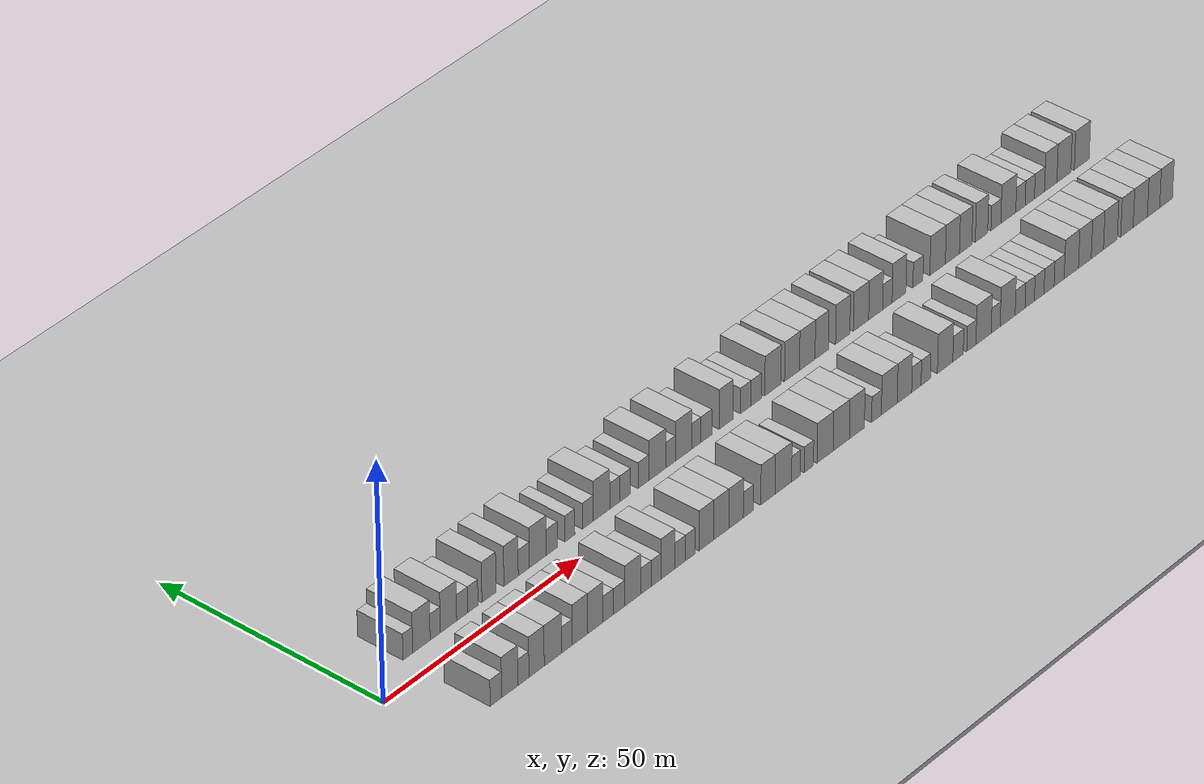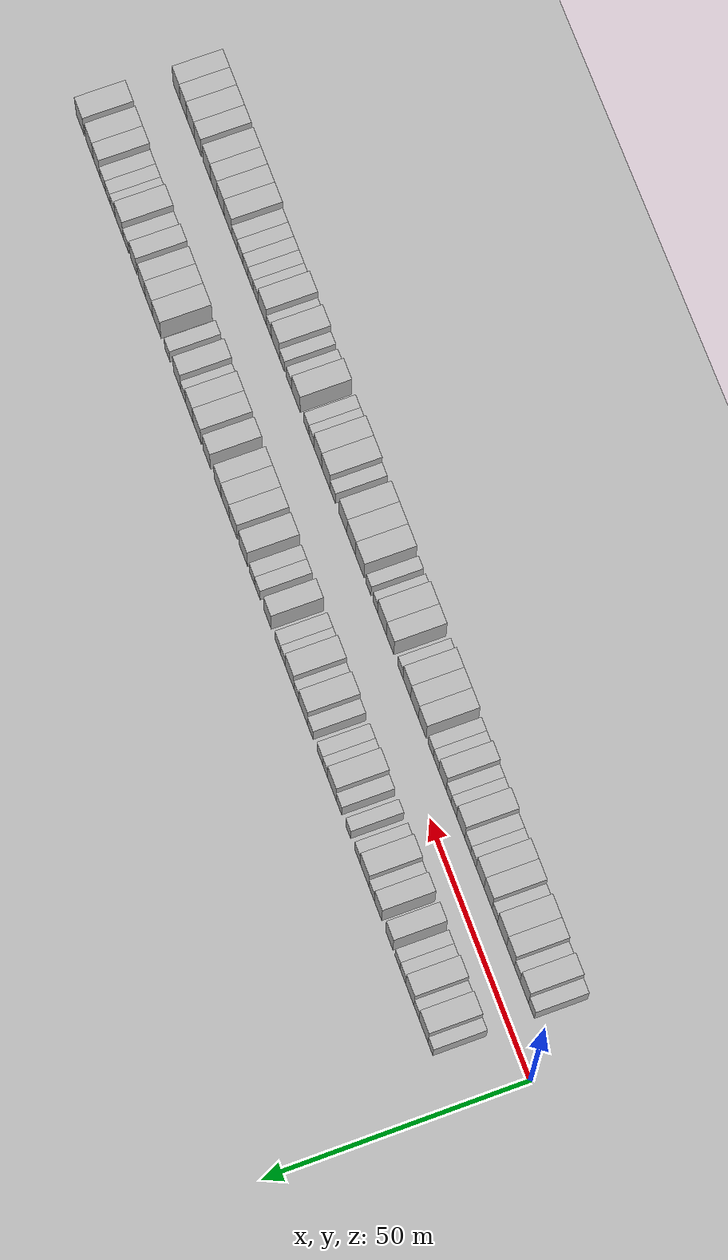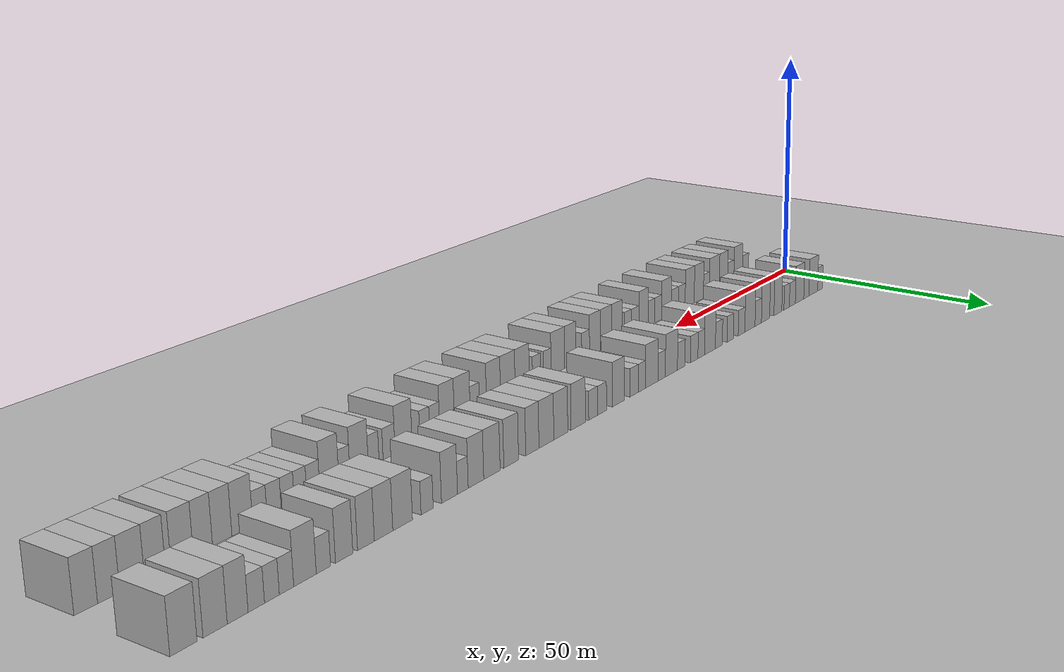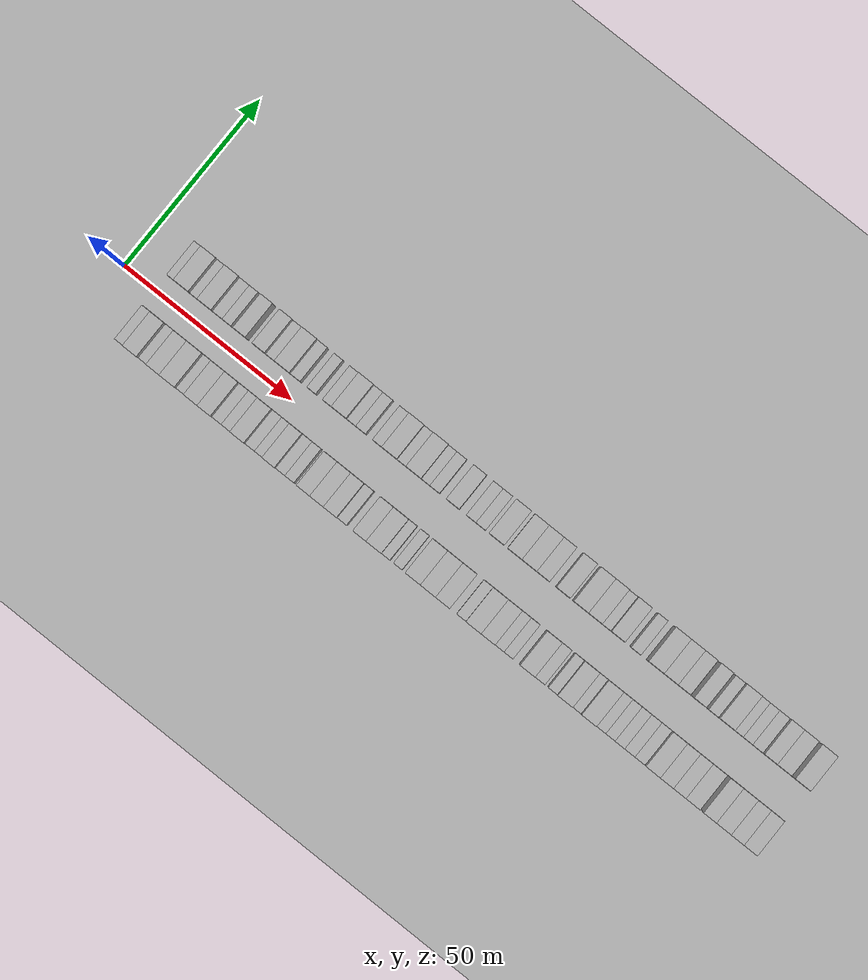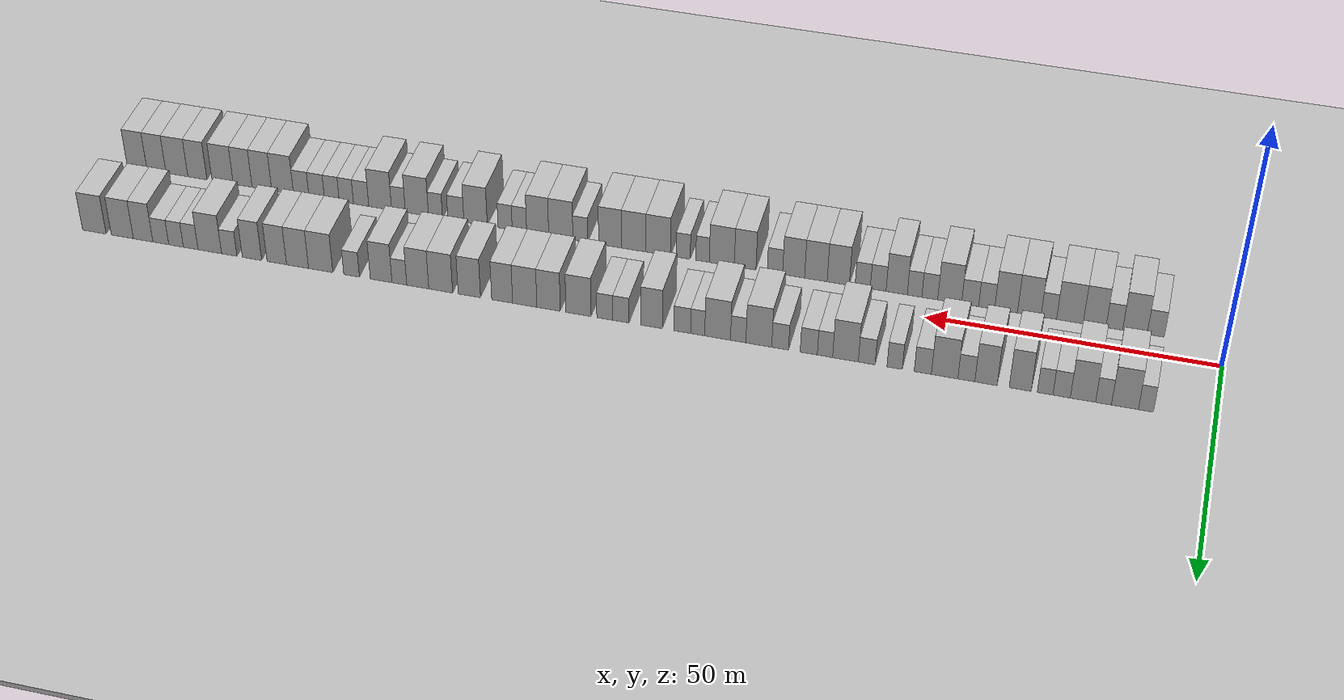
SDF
<?xml version="1.0" encoding="utf-8"?>

<sdf version="1.6">

   <world name="default">

      <gui fullscreen="0">

         <camera name="user_camera">

            <pose>-15 0 4.57585 0 0 0</pose>

            <view_controller>orbit</view_controller>

         </camera>

      </gui>

      <scene>

         <sky>

           <clouds>

             <speed>12</speed>

           </clouds>

         </sky>

         <ambient>0.4 0.4 0.4 1</ambient>

         <background>0.7 0.7 0.7 1</background>

         <shadows>1</shadows>

      </scene>

      <gravity>0 0 -9.8066</gravity>

      <magnetic_field>6e-06 2.3e-05 -4.2e-05</magnetic_field>

      <physics default="0" name="default_physics" type="ode">

         <ode>

            <solver>

               <type>quick</type>

               <iters>10</iters>

               <sor>1.0</sor>

               <use_dynamic_moi_rescaling>0</use_dynamic_moi_rescaling>

            </solver>

            <constraints>

               <cfm>0</cfm>

               <erp>0.2</erp>

               <contact_max_correcting_vel>100</contact_max_correcting_vel>

               <contact_surface_layer>0.001</contact_surface_layer>

            </constraints>

         </ode>

         <max_step_size>0.004</max_step_size>

         <real_time_factor>1</real_time_factor>

         <real_time_update_rate>250</real_time_update_rate>

      </physics>

      <light name="sun" type="directional">

         <cast_shadows>1</cast_shadows>

         <pose>0 0 10 0 0 0</pose>

         <diffuse>0.8 0.8 0.8 1</diffuse>

         <specular>0.2 0.2 0.2 1</specular>

         <attenuation>

            <range>1000</range>

            <constant>0.9</constant>

            <linear>0.01</linear>

            <quadratic>0.001</quadratic>

         </attenuation>

         <direction>-0.5 0.1 -0.9</direction>

      </light>

      <include>

         <name>ground_plane_1</name>

         <uri>model://HANNAS_ground_plane</uri>

         <pose>0 0 0  0 0 0</pose>

      </include>

      <include>

         <name>ground_plane_2</name>

         <uri>model://HANNAS_ground_plane</uri>

         <pose>100 0 0  0 0 0</pose>

      </include>

      <model name="building_1">

         <static>1</static>

         <pose frame="">11.2225 9.5000 0 0.000000 0.000000 1.570796</pose>

         <link name="link">

            <pose frame="">0 0 3.00 0 0 0</pose>

            <collision name="collision">

               <geometry>

                  <box>

                     <size>10.0000 2.4450 6.0000</size>

                  </box>

               </geometry>

               <max_contacts>10</max_contacts>

               <surface>

                  <contact>

                     <ode/>

                  </contact>

                  <bounce/>

                  <friction>

                     <torsional>

                        <ode/>

                     </torsional>

                     <ode/>

                  </friction>

               </surface>

            </collision>

            <visual name="visual">

               <cast_shadows>0</cast_shadows>

               <geometry>

                  <box>

                     <size>10.0000 2.4450 6.0000</size>

                  </box>

               </geometry>

               <material>

                  <script>

                     <uri>model://HANNAS_wall/materials/scripts</uri>

                     <uri>model://HANNAS_wall/materials/textures</uri>

                     <name>vrc/HANNAS_wall</name>

                  </script>

               </material>

            </visual>

            <self_collide>0</self_collide>

            <enable_wind>0</enable_wind>

            <kinematic>0</kinematic>

         </link>

      </model>

      <model name="building_2">

         <static>1</static>

         <pose frame="">14.6333 9.5000 0 0.000000 0.000000 1.570796</pose>

         <link name="link">

            <pose frame="">0 0 4.50 0 0 0</pose>

            <collision name="collision">

               <geometry>

                  <box>

                     <size>10.0000 4.3764 9.0000</size>

                  </box>

               </geometry>

               <max_contacts>10</max_contacts>

               <surface>

                  <contact>

                     <ode/>

                  </contact>

                  <bounce/>

                  <friction>

                     <torsional>

                        <ode/>

                     </torsional>

                     <ode/>

                  </friction>

               </surface>

            </collision>

            <visual name="visual">

               <cast_shadows>0</cast_shadows>

               <geometry>

                  <box>

                     <size>10.0000 4.3764 9.0000</size>

                  </box>

               </geometry>

               <material>

                  <script>

                     <uri>model://HANNAS_wall/materials/scripts</uri>

                     <uri>model://HANNAS_wall/materials/textures</uri>

                     <name>vrc/HANNAS_wall</name>

                  </script>

               </material>

            </visual>

            <self_collide>0</self_collide>

            <enable_wind>0</enable_wind>

            <kinematic>0</kinematic>

         </link>

      </model>

      <model name="building_3">

         <static>1</static>

         <pose frame="">18.1173 9.5000 0 0.000000 0.000000 1.570796</pose>

         <link name="link">

            <pose frame="">0 0 3.00 0 0 0</pose>

            <collision name="collision">

               <geometry>

                  <box>

                     <size>10.0000 2.5916 6.0000</size>

                  </box>

               </geometry>

               <max_contacts>10</max_contacts>

               <surface>

                  <contact>

                     <ode/>

                  </contact>

                  <bounce/>

                  <friction>

                     <torsional>

                        <ode/>

                     </torsional>

                     <ode/>

                  </friction>

               </surface>

            </collision>

            <visual name="visual">

               <cast_shadows>0</cast_shadows>

               <geometry>

                  <box>

                     <size>10.0000 2.5916 6.0000</size>

                  </box>

               </geometry>

               <material>

                  <script>

                     <uri>model://HANNAS_wall/materials/scripts</uri>

                     <uri>model://HANNAS_wall/materials/textures</uri>

                     <name>vrc/HANNAS_wall</name>

                  </script>

               </material>

            </visual>

            <self_collide>0</self_collide>

            <enable_wind>0</enable_wind>

            <kinematic>0</kinematic>

         </link>

      </model>

      <model name="building_4">

         <static>1</static>

         <pose frame="">21.4784 9.5000 0 0.000000 0.000000 1.570796</pose>

         <link name="link">

            <pose frame="">0 0 4.50 0 0 0</pose>

            <collision name="collision">

               <geometry>

                  <box>

                     <size>10.0000 4.1306 9.0000</size>

                  </box>

               </geometry>

               <max_contacts>10</max_contacts>

               <surface>

                  <contact>

                     <ode/>

                  </contact>

                  <bounce/>

                  <friction>

                     <torsional>

                        <ode/>

                     </torsional>

                     <ode/>

                  </friction>

               </surface>

            </collision>

            <visual name="visual">

               <cast_shadows>0</cast_shadows>

               <geometry>

                  <box>

                     <size>10.0000 4.1306 9.0000</size>

                  </box>

               </geometry>

               <material>

                  <script>

                     <uri>model://HANNAS_wall/materials/scripts</uri>

                     <uri>model://HANNAS_wall/materials/textures</uri>

                     <name>vrc/HANNAS_wall</name>

                  </script>

               </material>

            </visual>

            <self_collide>0</self_collide>

            <enable_wind>0</enable_wind>

            <kinematic>0</kinematic>

         </link>

      </model>

      <model name="building_5">

         <static>1</static>

         <pose frame="">24.9693 9.5000 0 0.000000 0.000000 1.570796</pose>

         <link name="link">

            <pose frame="">0 0 3.00 0 0 0</pose>

            <collision name="collision">

               <geometry>

                  <box>

                     <size>10.0000 2.8512 6.0000</size>

                  </box>

               </geometry>

               <max_contacts>10</max_contacts>

               <surface>

                  <contact>

                     <ode/>

                  </contact>

                  <bounce/>

                  <friction>

                     <torsional>

                        <ode/>

                     </torsional>

                     <ode/>

                  </friction>

               </surface>

            </collision>

            <visual name="visual">

               <cast_shadows>0</cast_shadows>

               <geometry>

                  <box>

                     <size>10.0000 2.8512 6.0000</size>

                  </box>

               </geometry>

               <material>

                  <script>

                     <uri>model://HANNAS_wall/materials/scripts</uri>

                     <uri>model://HANNAS_wall/materials/textures</uri>

                     <name>vrc/HANNAS_wall</name>

                  </script>

               </material>

            </visual>

            <self_collide>0</self_collide>

            <enable_wind>0</enable_wind>

            <kinematic>0</kinematic>

         </link>

      </model>

      <model name="building_6">

         <static>1</static>

         <pose frame="">27.6801 9.5000 0 0.000000 0.000000 1.570796</pose>

         <link name="link">

            <pose frame="">0 0 3.00 0 0 0</pose>

            <collision name="collision">

               <geometry>

                  <box>

                     <size>10.0000 2.5704 6.0000</size>

                  </box>

               </geometry>

               <max_contacts>10</max_contacts>

               <surface>

                  <contact>

                     <ode/>

                  </contact>

                  <bounce/>

                  <friction>

                     <torsional>

                        <ode/>

                     </torsional>

                     <ode/>

                  </friction>

               </surface>

            </collision>

            <visual name="visual">

               <cast_shadows>0</cast_shadows>

               <geometry>

                  <box>

                     <size>10.0000 2.5704 6.0000</size>

                  </box>

               </geometry>

               <material>

                  <script>

                     <uri>model://HANNAS_wall/materials/scripts</uri>

                     <uri>model://HANNAS_wall/materials/textures</uri>

                     <name>vrc/HANNAS_wall</name>

                  </script>

               </material>

            </visual>

            <self_collide>0</self_collide>

            <enable_wind>0</enable_wind>

            <kinematic>0</kinematic>

         </link>

      </model>

      <model name="building_7">

         <static>1</static>

         <pose frame="">31.7829 9.5000 0 0.000000 0.000000 1.570796</pose>

         <link name="link">

            <pose frame="">0 0 4.50 0 0 0</pose>

            <collision name="collision">

               <geometry>

                  <box>

                     <size>10.0000 3.6352 9.0000</size>

                  </box>

               </geometry>

               <max_contacts>10</max_contacts>

               <surface>

                  <contact>

                     <ode/>

                  </contact>

                  <bounce/>

                  <friction>

                     <torsional>

                        <ode/>

                     </torsional>

                     <ode/>

                  </friction>

               </surface>

            </collision>

            <visual name="visual">

               <cast_shadows>0</cast_shadows>

               <geometry>

                  <box>

                     <size>10.0000 3.6352 9.0000</size>

                  </box>

               </geometry>

               <material>

                  <script>

                     <uri>model://HANNAS_wall/materials/scripts</uri>

                     <uri>model://HANNAS_wall/materials/textures</uri>

                     <name>vrc/HANNAS_wall</name>

                  </script>

               </material>

            </visual>

            <self_collide>0</self_collide>

            <enable_wind>0</enable_wind>

            <kinematic>0</kinematic>

         </link>

      </model>

      <model name="building_8">

         <static>1</static>

         <pose frame="">37.4453 9.5000 0 0.000000 0.000000 1.570796</pose>

         <link name="link">

            <pose frame="">0 0 4.50 0 0 0</pose>

            <collision name="collision">

               <geometry>

                  <box>

                     <size>10.0000 3.6897 9.0000</size>

                  </box>

               </geometry>

               <max_contacts>10</max_contacts>

               <surface>

                  <contact>

                     <ode/>

                  </contact>

                  <bounce/>

                  <friction>

                     <torsional>

                        <ode/>

                     </torsional>

                     <ode/>

                  </friction>

               </surface>

            </collision>

            <visual name="visual">

               <cast_shadows>0</cast_shadows>

               <geometry>

                  <box>

                     <size>10.0000 3.6897 9.0000</size>

                  </box>

               </geometry>

               <material>

                  <script>

                     <uri>model://HANNAS_wall/materials/scripts</uri>

                     <uri>model://HANNAS_wall/materials/textures</uri>

                     <name>vrc/HANNAS_wall</name>

                  </script>

               </material>

            </visual>

            <self_collide>0</self_collide>

            <enable_wind>0</enable_wind>

            <kinematic>0</kinematic>

         </link>

      </model>

      <model name="building_9">

         <static>1</static>

         <pose frame="">40.7067 9.5000 0 0.000000 0.000000 1.570796</pose>

         <link name="link">

            <pose frame="">0 0 3.00 0 0 0</pose>

            <collision name="collision">

               <geometry>

                  <box>

                     <size>10.0000 2.8331 6.0000</size>

                  </box>

               </geometry>

               <max_contacts>10</max_contacts>

               <surface>

                  <contact>

                     <ode/>

                  </contact>

                  <bounce/>

                  <friction>

                     <torsional>

                        <ode/>

                     </torsional>

                     <ode/>

                  </friction>

               </surface>

            </collision>

            <visual name="visual">

               <cast_shadows>0</cast_shadows>

               <geometry>

                  <box>

                     <size>10.0000 2.8331 6.0000</size>

                  </box>

               </geometry>

               <material>

                  <script>

                     <uri>model://HANNAS_wall/materials/scripts</uri>

                     <uri>model://HANNAS_wall/materials/textures</uri>

                     <name>vrc/HANNAS_wall</name>

                  </script>

               </material>

            </visual>

            <self_collide>0</self_collide>

            <enable_wind>0</enable_wind>

            <kinematic>0</kinematic>

         </link>

      </model>

      <model name="building_10">

         <static>1</static>

         <pose frame="">44.3347 9.5000 0 0.000000 0.000000 1.570796</pose>

         <link name="link">

            <pose frame="">0 0 4.50 0 0 0</pose>

            <collision name="collision">

               <geometry>

                  <box>

                     <size>10.0000 4.4229 9.0000</size>

                  </box>

               </geometry>

               <max_contacts>10</max_contacts>

               <surface>

                  <contact>

                     <ode/>

                  </contact>

                  <bounce/>

                  <friction>

                     <torsional>

                        <ode/>

                     </torsional>

                     <ode/>

                  </friction>

               </surface>

            </collision>

            <visual name="visual">

               <cast_shadows>0</cast_shadows>

               <geometry>

                  <box>

                     <size>10.0000 4.4229 9.0000</size>

                  </box>

               </geometry>

               <material>

                  <script>

                     <uri>model://HANNAS_wall/materials/scripts</uri>

                     <uri>model://HANNAS_wall/materials/textures</uri>

                     <name>vrc/HANNAS_wall</name>

                  </script>

               </material>

            </visual>

            <self_collide>0</self_collide>

            <enable_wind>0</enable_wind>

            <kinematic>0</kinematic>

         </link>

      </model>

      <model name="building_11">

         <static>1</static>

         <pose frame="">47.9818 9.5000 0 0.000000 0.000000 1.570796</pose>

         <link name="link">

            <pose frame="">0 0 3.00 0 0 0</pose>

            <collision name="collision">

               <geometry>

                  <box>

                     <size>10.0000 2.8714 6.0000</size>

                  </box>

               </geometry>

               <max_contacts>10</max_contacts>

               <surface>

                  <contact>

                     <ode/>

                  </contact>

                  <bounce/>

                  <friction>

                     <torsional>

                        <ode/>

                     </torsional>

                     <ode/>

                  </friction>

               </surface>

            </collision>

            <visual name="visual">

               <cast_shadows>0</cast_shadows>

               <geometry>

                  <box>

                     <size>10.0000 2.8714 6.0000</size>

                  </box>

               </geometry>

               <material>

                  <script>

                     <uri>model://HANNAS_wall/materials/scripts</uri>

                     <uri>model://HANNAS_wall/materials/textures</uri>

                     <name>vrc/HANNAS_wall</name>

                  </script>

               </material>

            </visual>

            <self_collide>0</self_collide>

            <enable_wind>0</enable_wind>

            <kinematic>0</kinematic>

         </link>

      </model>

      <model name="building_12">

         <static>1</static>

         <pose frame="">52.7090 9.5000 0 0.000000 0.000000 1.570796</pose>

         <link name="link">

            <pose frame="">0 0 3.00 0 0 0</pose>

            <collision name="collision">

               <geometry>

                  <box>

                     <size>10.0000 2.5830 6.0000</size>

                  </box>

               </geometry>

               <max_contacts>10</max_contacts>

               <surface>

                  <contact>

                     <ode/>

                  </contact>

                  <bounce/>

                  <friction>

                     <torsional>

                        <ode/>

                     </torsional>

                     <ode/>

                  </friction>

               </surface>

            </collision>

            <visual name="visual">

               <cast_shadows>0</cast_shadows>

               <geometry>

                  <box>

                     <size>10.0000 2.5830 6.0000</size>

                  </box>

               </geometry>

               <material>

                  <script>

                     <uri>model://HANNAS_wall/materials/scripts</uri>

                     <uri>model://HANNAS_wall/materials/textures</uri>

                     <name>vrc/HANNAS_wall</name>

                  </script>

               </material>

            </visual>

            <self_collide>0</self_collide>

            <enable_wind>0</enable_wind>

            <kinematic>0</kinematic>

         </link>

      </model>

      <model name="building_13">

         <static>1</static>

         <pose frame="">57.4176 9.5000 0 0.000000 0.000000 1.570796</pose>

         <link name="link">

            <pose frame="">0 0 3.00 0 0 0</pose>

            <collision name="collision">

               <geometry>

                  <box>

                     <size>10.0000 2.8341 6.0000</size>

                  </box>

               </geometry>

               <max_contacts>10</max_contacts>

               <surface>

                  <contact>

                     <ode/>

                  </contact>

                  <bounce/>

                  <friction>

                     <torsional>

                        <ode/>

                     </torsional>

                     <ode/>

                  </friction>

               </surface>

            </collision>

            <visual name="visual">

               <cast_shadows>0</cast_shadows>

               <geometry>

                  <box>

                     <size>10.0000 2.8341 6.0000</size>

                  </box>

               </geometry>

               <material>

                  <script>

                     <uri>model://HANNAS_wall/materials/scripts</uri>

                     <uri>model://HANNAS_wall/materials/textures</uri>

                     <name>vrc/HANNAS_wall</name>

                  </script>

               </material>

            </visual>

            <self_collide>0</self_collide>

            <enable_wind>0</enable_wind>

            <kinematic>0</kinematic>

         </link>

      </model>

      <model name="building_14">

         <static>1</static>

         <pose frame="">61.0146 9.5000 0 0.000000 0.000000 1.570796</pose>

         <link name="link">

            <pose frame="">0 0 4.50 0 0 0</pose>

            <collision name="collision">

               <geometry>

                  <box>

                     <size>10.0000 4.3599 9.0000</size>

                  </box>

               </geometry>

               <max_contacts>10</max_contacts>

               <surface>

                  <contact>

                     <ode/>

                  </contact>

                  <bounce/>

                  <friction>

                     <torsional>

                        <ode/>

                     </torsional>

                     <ode/>

                  </friction>

               </surface>

            </collision>

            <visual name="visual">

               <cast_shadows>0</cast_shadows>

               <geometry>

                  <box>

                     <size>10.0000 4.3599 9.0000</size>

                  </box>

               </geometry>

               <material>

                  <script>

                     <uri>model://HANNAS_wall/materials/scripts</uri>

                     <uri>model://HANNAS_wall/materials/textures</uri>

                     <name>vrc/HANNAS_wall</name>

                  </script>

               </material>

            </visual>

            <self_collide>0</self_collide>

            <enable_wind>0</enable_wind>

            <kinematic>0</kinematic>

         </link>

      </model>

      <model name="building_15">

         <static>1</static>

         <pose frame="">64.4956 9.5000 0 0.000000 0.000000 1.570796</pose>

         <link name="link">

            <pose frame="">0 0 3.00 0 0 0</pose>

            <collision name="collision">

               <geometry>

                  <box>

                     <size>10.0000 2.6021 6.0000</size>

                  </box>

               </geometry>

               <max_contacts>10</max_contacts>

               <surface>

                  <contact>

                     <ode/>

                  </contact>

                  <bounce/>

                  <friction>

                     <torsional>

                        <ode/>

                     </torsional>

                     <ode/>

                  </friction>

               </surface>

            </collision>

            <visual name="visual">

               <cast_shadows>0</cast_shadows>

               <geometry>

                  <box>

                     <size>10.0000 2.6021 6.0000</size>

                  </box>

               </geometry>

               <material>

                  <script>

                     <uri>model://HANNAS_wall/materials/scripts</uri>

                     <uri>model://HANNAS_wall/materials/textures</uri>

                     <name>vrc/HANNAS_wall</name>

                  </script>

               </material>

            </visual>

            <self_collide>0</self_collide>

            <enable_wind>0</enable_wind>

            <kinematic>0</kinematic>

         </link>

      </model>

      <model name="building_16">

         <static>1</static>

         <pose frame="">67.2565 9.5000 0 0.000000 0.000000 1.570796</pose>

         <link name="link">

            <pose frame="">0 0 3.00 0 0 0</pose>

            <collision name="collision">

               <geometry>

                  <box>

                     <size>10.0000 2.9195 6.0000</size>

                  </box>

               </geometry>

               <max_contacts>10</max_contacts>

               <surface>

                  <contact>

                     <ode/>

                  </contact>

                  <bounce/>

                  <friction>

                     <torsional>

                        <ode/>

                     </torsional>

                     <ode/>

                  </friction>

               </surface>

            </collision>

            <visual name="visual">

               <cast_shadows>0</cast_shadows>

               <geometry>

                  <box>

                     <size>10.0000 2.9195 6.0000</size>

                  </box>

               </geometry>

               <material>

                  <script>

                     <uri>model://HANNAS_wall/materials/scripts</uri>

                     <uri>model://HANNAS_wall/materials/textures</uri>

                     <name>vrc/HANNAS_wall</name>

                  </script>

               </material>

            </visual>

            <self_collide>0</self_collide>

            <enable_wind>0</enable_wind>

            <kinematic>0</kinematic>

         </link>

      </model>

      <model name="building_17">

         <static>1</static>

         <pose frame="">72.1539 9.5000 0 0.000000 0.000000 1.570796</pose>

         <link name="link">

            <pose frame="">0 0 3.00 0 0 0</pose>

            <collision name="collision">

               <geometry>

                  <box>

                     <size>10.0000 2.8754 6.0000</size>

                  </box>

               </geometry>

               <max_contacts>10</max_contacts>

               <surface>

                  <contact>

                     <ode/>

                  </contact>

                  <bounce/>

                  <friction>

                     <torsional>

                        <ode/>

                     </torsional>

                     <ode/>

                  </friction>

               </surface>

            </collision>

            <visual name="visual">

               <cast_shadows>0</cast_shadows>

               <geometry>

                  <box>

                     <size>10.0000 2.8754 6.0000</size>

                  </box>

               </geometry>

               <material>

                  <script>

                     <uri>model://HANNAS_wall/materials/scripts</uri>

                     <uri>model://HANNAS_wall/materials/textures</uri>

                     <name>vrc/HANNAS_wall</name>

                  </script>

               </material>

            </visual>

            <self_collide>0</self_collide>

            <enable_wind>0</enable_wind>

            <kinematic>0</kinematic>

         </link>

      </model>

      <model name="building_18">

         <static>1</static>

         <pose frame="">75.8124 9.5000 0 0.000000 0.000000 1.570796</pose>

         <link name="link">

            <pose frame="">0 0 4.50 0 0 0</pose>

            <collision name="collision">

               <geometry>

                  <box>

                     <size>10.0000 4.4415 9.0000</size>

                  </box>

               </geometry>

               <max_contacts>10</max_contacts>

               <surface>

                  <contact>

                     <ode/>

                  </contact>

                  <bounce/>

                  <friction>

                     <torsional>

                        <ode/>

                     </torsional>

                     <ode/>

                  </friction>

               </surface>

            </collision>

            <visual name="visual">

               <cast_shadows>0</cast_shadows>

               <geometry>

                  <box>

                     <size>10.0000 4.4415 9.0000</size>

                  </box>

               </geometry>

               <material>

                  <script>

                     <uri>model://HANNAS_wall/materials/scripts</uri>

                     <uri>model://HANNAS_wall/materials/textures</uri>

                     <name>vrc/HANNAS_wall</name>

                  </script>

               </material>

            </visual>

            <self_collide>0</self_collide>

            <enable_wind>0</enable_wind>

            <kinematic>0</kinematic>

         </link>

      </model>

      <model name="building_19">

         <static>1</static>

         <pose frame="">79.3534 9.5000 0 0.000000 0.000000 1.570796</pose>

         <link name="link">

            <pose frame="">0 0 3.00 0 0 0</pose>

            <collision name="collision">

               <geometry>

                  <box>

                     <size>10.0000 2.6405 6.0000</size>

                  </box>

               </geometry>

               <max_contacts>10</max_contacts>

               <surface>

                  <contact>

                     <ode/>

                  </contact>

                  <bounce/>

                  <friction>

                     <torsional>

                        <ode/>

                     </torsional>

                     <ode/>

                  </friction>

               </surface>

            </collision>

            <visual name="visual">

               <cast_shadows>0</cast_shadows>

               <geometry>

                  <box>

                     <size>10.0000 2.6405 6.0000</size>

                  </box>

               </geometry>

               <material>

                  <script>

                     <uri>model://HANNAS_wall/materials/scripts</uri>

                     <uri>model://HANNAS_wall/materials/textures</uri>

                     <name>vrc/HANNAS_wall</name>

                  </script>

               </material>

            </visual>

            <self_collide>0</self_collide>

            <enable_wind>0</enable_wind>

            <kinematic>0</kinematic>

         </link>

      </model>

      <model name="building_20">

         <static>1</static>

         <pose frame="">82.9072 9.5000 0 0.000000 0.000000 1.570796</pose>

         <link name="link">

            <pose frame="">0 0 4.50 0 0 0</pose>

            <collision name="collision">

               <geometry>

                  <box>

                     <size>10.0000 4.4671 9.0000</size>

                  </box>

               </geometry>

               <max_contacts>10</max_contacts>

               <surface>

                  <contact>

                     <ode/>

                  </contact>

                  <bounce/>

                  <friction>

                     <torsional>

                        <ode/>

                     </torsional>

                     <ode/>

                  </friction>

               </surface>

            </collision>

            <visual name="visual">

               <cast_shadows>0</cast_shadows>

               <geometry>

                  <box>

                     <size>10.0000 4.4671 9.0000</size>

                  </box>

               </geometry>

               <material>

                  <script>

                     <uri>model://HANNAS_wall/materials/scripts</uri>

                     <uri>model://HANNAS_wall/materials/textures</uri>

                     <name>vrc/HANNAS_wall</name>

                  </script>

               </material>

            </visual>

            <self_collide>0</self_collide>

            <enable_wind>0</enable_wind>

            <kinematic>0</kinematic>

         </link>

      </model>

      <model name="building_21">

         <static>1</static>

         <pose frame="">86.3686 9.5000 0 0.000000 0.000000 1.570796</pose>

         <link name="link">

            <pose frame="">0 0 3.00 0 0 0</pose>

            <collision name="collision">

               <geometry>

                  <box>

                     <size>10.0000 2.4558 6.0000</size>

                  </box>

               </geometry>

               <max_contacts>10</max_contacts>

               <surface>

                  <contact>

                     <ode/>

                  </contact>

                  <bounce/>

                  <friction>

                     <torsional>

                        <ode/>

                     </torsional>

                     <ode/>

                  </friction>

               </surface>

            </collision>

            <visual name="visual">

               <cast_shadows>0</cast_shadows>

               <geometry>

                  <box>

                     <size>10.0000 2.4558 6.0000</size>

                  </box>

               </geometry>

               <material>

                  <script>

                     <uri>model://HANNAS_wall/materials/scripts</uri>

                     <uri>model://HANNAS_wall/materials/textures</uri>

                     <name>vrc/HANNAS_wall</name>

                  </script>

               </material>

            </visual>

            <self_collide>0</self_collide>

            <enable_wind>0</enable_wind>

            <kinematic>0</kinematic>

         </link>

      </model>

      <model name="building_22">

         <static>1</static>

         <pose frame="">89.0423 9.5000 0 0.000000 0.000000 1.570796</pose>

         <link name="link">

            <pose frame="">0 0 3.00 0 0 0</pose>

            <collision name="collision">

               <geometry>

                  <box>

                     <size>10.0000 2.8916 6.0000</size>

                  </box>

               </geometry>

               <max_contacts>10</max_contacts>

               <surface>

                  <contact>

                     <ode/>

                  </contact>

                  <bounce/>

                  <friction>

                     <torsional>

                        <ode/>

                     </torsional>

                     <ode/>

                  </friction>

               </surface>

            </collision>

            <visual name="visual">

               <cast_shadows>0</cast_shadows>

               <geometry>

                  <box>

                     <size>10.0000 2.8916 6.0000</size>

                  </box>

               </geometry>

               <material>

                  <script>

                     <uri>model://HANNAS_wall/materials/scripts</uri>

                     <uri>model://HANNAS_wall/materials/textures</uri>

                     <name>vrc/HANNAS_wall</name>

                  </script>

               </material>

            </visual>

            <self_collide>0</self_collide>

            <enable_wind>0</enable_wind>

            <kinematic>0</kinematic>

         </link>

      </model>

      <model name="building_23">

         <static>1</static>

         <pose frame="">94.4059 9.5000 0 0.000000 0.000000 1.570796</pose>

         <link name="link">

            <pose frame="">0 0 4.50 0 0 0</pose>

            <collision name="collision">

               <geometry>

                  <box>

                     <size>10.0000 3.8355 9.0000</size>

                  </box>

               </geometry>

               <max_contacts>10</max_contacts>

               <surface>

                  <contact>

                     <ode/>

                  </contact>

                  <bounce/>

                  <friction>

                     <torsional>

                        <ode/>

                     </torsional>

                     <ode/>

                  </friction>

               </surface>

            </collision>

            <visual name="visual">

               <cast_shadows>0</cast_shadows>

               <geometry>

                  <box>

                     <size>10.0000 3.8355 9.0000</size>

                  </box>

               </geometry>

               <material>

                  <script>

                     <uri>model://HANNAS_wall/materials/scripts</uri>

                     <uri>model://HANNAS_wall/materials/textures</uri>

                     <name>vrc/HANNAS_wall</name>

                  </script>

               </material>

            </visual>

            <self_collide>0</self_collide>

            <enable_wind>0</enable_wind>

            <kinematic>0</kinematic>

         </link>

      </model>

      <model name="building_24">

         <static>1</static>

         <pose frame="">99.7454 9.5000 0 0.000000 0.000000 1.570796</pose>

         <link name="link">

            <pose frame="">0 0 3.00 0 0 0</pose>

            <collision name="collision">

               <geometry>

                  <box>

                     <size>10.0000 2.8435 6.0000</size>

                  </box>

               </geometry>

               <max_contacts>10</max_contacts>

               <surface>

                  <contact>

                     <ode/>

                  </contact>

                  <bounce/>

                  <friction>

                     <torsional>

                        <ode/>

                     </torsional>

                     <ode/>

                  </friction>

               </surface>

            </collision>

            <visual name="visual">

               <cast_shadows>0</cast_shadows>

               <geometry>

                  <box>

                     <size>10.0000 2.8435 6.0000</size>

                  </box>

               </geometry>

               <material>

                  <script>

                     <uri>model://HANNAS_wall/materials/scripts</uri>

                     <uri>model://HANNAS_wall/materials/textures</uri>

                     <name>vrc/HANNAS_wall</name>

                  </script>

               </material>

            </visual>

            <self_collide>0</self_collide>

            <enable_wind>0</enable_wind>

            <kinematic>0</kinematic>

         </link>

      </model>

      <model name="building_25">

         <static>1</static>

         <pose frame="">102.5829 9.5000 0 0.000000 0.000000 1.570796</pose>

         <link name="link">

            <pose frame="">0 0 3.00 0 0 0</pose>

            <collision name="collision">

               <geometry>

                  <box>

                     <size>10.0000 2.8314 6.0000</size>

                  </box>

               </geometry>

               <max_contacts>10</max_contacts>

               <surface>

                  <contact>

                     <ode/>

                  </contact>

                  <bounce/>

                  <friction>

                     <torsional>

                        <ode/>

                     </torsional>

                     <ode/>

                  </friction>

               </surface>

            </collision>

            <visual name="visual">

               <cast_shadows>0</cast_shadows>

               <geometry>

                  <box>

                     <size>10.0000 2.8314 6.0000</size>

                  </box>

               </geometry>

               <material>

                  <script>

                     <uri>model://HANNAS_wall/materials/scripts</uri>

                     <uri>model://HANNAS_wall/materials/textures</uri>

                     <name>vrc/HANNAS_wall</name>

                  </script>

               </material>

            </visual>

            <self_collide>0</self_collide>

            <enable_wind>0</enable_wind>

            <kinematic>0</kinematic>

         </link>

      </model>

      <model name="building_26">

         <static>1</static>

         <pose frame="">107.2261 9.5000 0 0.000000 0.000000 1.570796</pose>

         <link name="link">

            <pose frame="">0 0 4.50 0 0 0</pose>

            <collision name="collision">

               <geometry>

                  <box>

                     <size>10.0000 4.4551 9.0000</size>

                  </box>

               </geometry>

               <max_contacts>10</max_contacts>

               <surface>

                  <contact>

                     <ode/>

                  </contact>

                  <bounce/>

                  <friction>

                     <torsional>

                        <ode/>

                     </torsional>

                     <ode/>

                  </friction>

               </surface>

            </collision>

            <visual name="visual">

               <cast_shadows>0</cast_shadows>

               <geometry>

                  <box>

                     <size>10.0000 4.4551 9.0000</size>

                  </box>

               </geometry>

               <material>

                  <script>

                     <uri>model://HANNAS_wall/materials/scripts</uri>

                     <uri>model://HANNAS_wall/materials/textures</uri>

                     <name>vrc/HANNAS_wall</name>

                  </script>

               </material>

            </visual>

            <self_collide>0</self_collide>

            <enable_wind>0</enable_wind>

            <kinematic>0</kinematic>

         </link>

      </model>

      <model name="building_27">

         <static>1</static>

         <pose frame="">112.5299 9.5000 0 0.000000 0.000000 1.570796</pose>

         <link name="link">

            <pose frame="">0 0 4.50 0 0 0</pose>

            <collision name="collision">

               <geometry>

                  <box>

                     <size>10.0000 4.1524 9.0000</size>

                  </box>

               </geometry>

               <max_contacts>10</max_contacts>

               <surface>

                  <contact>

                     <ode/>

                  </contact>

                  <bounce/>

                  <friction>

                     <torsional>

                        <ode/>

                     </torsional>

                     <ode/>

                  </friction>

               </surface>

            </collision>

            <visual name="visual">

               <cast_shadows>0</cast_shadows>

               <geometry>

                  <box>

                     <size>10.0000 4.1524 9.0000</size>

                  </box>

               </geometry>

               <material>

                  <script>

                     <uri>model://HANNAS_wall/materials/scripts</uri>

                     <uri>model://HANNAS_wall/materials/textures</uri>

                     <name>vrc/HANNAS_wall</name>

                  </script>

               </material>

            </visual>

            <self_collide>0</self_collide>

            <enable_wind>0</enable_wind>

            <kinematic>0</kinematic>

         </link>

      </model>

      <model name="building_28">

         <static>1</static>

         <pose frame="">116.7682 9.5000 0 0.000000 0.000000 1.570796</pose>

         <link name="link">

            <pose frame="">0 0 4.50 0 0 0</pose>

            <collision name="collision">

               <geometry>

                  <box>

                     <size>10.0000 4.3243 9.0000</size>

                  </box>

               </geometry>

               <max_contacts>10</max_contacts>

               <surface>

                  <contact>

                     <ode/>

                  </contact>

                  <bounce/>

                  <friction>

                     <torsional>

                        <ode/>

                     </torsional>

                     <ode/>

                  </friction>

               </surface>

            </collision>

            <visual name="visual">

               <cast_shadows>0</cast_shadows>

               <geometry>

                  <box>

                     <size>10.0000 4.3243 9.0000</size>

                  </box>

               </geometry>

               <material>

                  <script>

                     <uri>model://HANNAS_wall/materials/scripts</uri>

                     <uri>model://HANNAS_wall/materials/textures</uri>

                     <name>vrc/HANNAS_wall</name>

                  </script>

               </material>

            </visual>

            <self_collide>0</self_collide>

            <enable_wind>0</enable_wind>

            <kinematic>0</kinematic>

         </link>

      </model>

      <model name="building_29">

         <static>1</static>

         <pose frame="">120.8029 9.5000 0 0.000000 0.000000 1.570796</pose>

         <link name="link">

            <pose frame="">0 0 4.50 0 0 0</pose>

            <collision name="collision">

               <geometry>

                  <box>

                     <size>10.0000 3.7449 9.0000</size>

                  </box>

               </geometry>

               <max_contacts>10</max_contacts>

               <surface>

                  <contact>

                     <ode/>

                  </contact>

                  <bounce/>

                  <friction>

                     <torsional>

                        <ode/>

                     </torsional>

                     <ode/>

                  </friction>

               </surface>

            </collision>

            <visual name="visual">

               <cast_shadows>0</cast_shadows>

               <geometry>

                  <box>

                     <size>10.0000 3.7449 9.0000</size>

                  </box>

               </geometry>

               <material>

                  <script>

                     <uri>model://HANNAS_wall/materials/scripts</uri>

                     <uri>model://HANNAS_wall/materials/textures</uri>

                     <name>vrc/HANNAS_wall</name>

                  </script>

               </material>

            </visual>

            <self_collide>0</self_collide>

            <enable_wind>0</enable_wind>

            <kinematic>0</kinematic>

         </link>

      </model>

      <model name="building_30">

         <static>1</static>

         <pose frame="">126.6835 9.5000 0 0.000000 0.000000 1.570796</pose>

         <link name="link">

            <pose frame="">0 0 4.50 0 0 0</pose>

            <collision name="collision">

               <geometry>

                  <box>

                     <size>10.0000 4.0163 9.0000</size>

                  </box>

               </geometry>

               <max_contacts>10</max_contacts>

               <surface>

                  <contact>

                     <ode/>

                  </contact>

                  <bounce/>

                  <friction>

                     <torsional>

                        <ode/>

                     </torsional>

                     <ode/>

                  </friction>

               </surface>

            </collision>

            <visual name="visual">

               <cast_shadows>0</cast_shadows>

               <geometry>

                  <box>

                     <size>10.0000 4.0163 9.0000</size>

                  </box>

               </geometry>

               <material>

                  <script>

                     <uri>model://HANNAS_wall/materials/scripts</uri>

                     <uri>model://HANNAS_wall/materials/textures</uri>

                     <name>vrc/HANNAS_wall</name>

                  </script>

               </material>

            </visual>

            <self_collide>0</self_collide>

            <enable_wind>0</enable_wind>

            <kinematic>0</kinematic>

         </link>

      </model>

      <model name="building_31">

         <static>1</static>

         <pose frame="">131.8514 9.5000 0 0.000000 0.000000 1.570796</pose>

         <link name="link">

            <pose frame="">0 0 4.50 0 0 0</pose>

            <collision name="collision">

               <geometry>

                  <box>

                     <size>10.0000 4.3196 9.0000</size>

                  </box>

               </geometry>

               <max_contacts>10</max_contacts>

               <surface>

                  <contact>

                     <ode/>

                  </contact>

                  <bounce/>

                  <friction>

                     <torsional>

                        <ode/>

                     </torsional>

                     <ode/>

                  </friction>

               </surface>

            </collision>

            <visual name="visual">

               <cast_shadows>0</cast_shadows>

               <geometry>

                  <box>

                     <size>10.0000 4.3196 9.0000</size>

                  </box>

               </geometry>

               <material>

                  <script>

                     <uri>model://HANNAS_wall/materials/scripts</uri>

                     <uri>model://HANNAS_wall/materials/textures</uri>

                     <name>vrc/HANNAS_wall</name>

                  </script>

               </material>

            </visual>

            <self_collide>0</self_collide>

            <enable_wind>0</enable_wind>

            <kinematic>0</kinematic>

         </link>

      </model>

      <model name="building_32">

         <static>1</static>

         <pose frame="">136.0064 9.5000 0 0.000000 0.000000 1.570796</pose>

         <link name="link">

            <pose frame="">0 0 4.50 0 0 0</pose>

            <collision name="collision">

               <geometry>

                  <box>

                     <size>10.0000 3.9903 9.0000</size>

                  </box>

               </geometry>

               <max_contacts>10</max_contacts>

               <surface>

                  <contact>

                     <ode/>

                  </contact>

                  <bounce/>

                  <friction>

                     <torsional>

                        <ode/>

                     </torsional>

                     <ode/>

                  </friction>

               </surface>

            </collision>

            <visual name="visual">

               <cast_shadows>0</cast_shadows>

               <geometry>

                  <box>

                     <size>10.0000 3.9903 9.0000</size>

                  </box>

               </geometry>

               <material>

                  <script>

                     <uri>model://HANNAS_wall/materials/scripts</uri>

                     <uri>model://HANNAS_wall/materials/textures</uri>

                     <name>vrc/HANNAS_wall</name>

                  </script>

               </material>

            </visual>

            <self_collide>0</self_collide>

            <enable_wind>0</enable_wind>

            <kinematic>0</kinematic>

         </link>

      </model>

      <model name="building_33">

         <static>1</static>

         <pose frame="">139.3425 9.5000 0 0.000000 0.000000 1.570796</pose>

         <link name="link">

            <pose frame="">0 0 3.00 0 0 0</pose>

            <collision name="collision">

               <geometry>

                  <box>

                     <size>10.0000 2.6820 6.0000</size>

                  </box>

               </geometry>

               <max_contacts>10</max_contacts>

               <surface>

                  <contact>

                     <ode/>

                  </contact>

                  <bounce/>

                  <friction>

                     <torsional>

                        <ode/>

                     </torsional>

                     <ode/>

                  </friction>

               </surface>

            </collision>

            <visual name="visual">

               <cast_shadows>0</cast_shadows>

               <geometry>

                  <box>

                     <size>10.0000 2.6820 6.0000</size>

                  </box>

               </geometry>

               <material>

                  <script>

                     <uri>model://HANNAS_wall/materials/scripts</uri>

                     <uri>model://HANNAS_wall/materials/textures</uri>

                     <name>vrc/HANNAS_wall</name>

                  </script>

               </material>

            </visual>

            <self_collide>0</self_collide>

            <enable_wind>0</enable_wind>

            <kinematic>0</kinematic>

         </link>

      </model>

      <model name="building_34">

         <static>1</static>

         <pose frame="">142.6555 9.5000 0 0.000000 0.000000 1.570796</pose>

         <link name="link">

            <pose frame="">0 0 4.50 0 0 0</pose>

            <collision name="collision">

               <geometry>

                  <box>

                     <size>10.0000 3.9439 9.0000</size>

                  </box>

               </geometry>

               <max_contacts>10</max_contacts>

               <surface>

                  <contact>

                     <ode/>

                  </contact>

                  <bounce/>

                  <friction>

                     <torsional>

                        <ode/>

                     </torsional>

                     <ode/>

                  </friction>

               </surface>

            </collision>

            <visual name="visual">

               <cast_shadows>0</cast_shadows>

               <geometry>

                  <box>

                     <size>10.0000 3.9439 9.0000</size>

                  </box>

               </geometry>

               <material>

                  <script>

                     <uri>model://HANNAS_wall/materials/scripts</uri>

                     <uri>model://HANNAS_wall/materials/textures</uri>

                     <name>vrc/HANNAS_wall</name>

                  </script>

               </material>

            </visual>

            <self_collide>0</self_collide>

            <enable_wind>0</enable_wind>

            <kinematic>0</kinematic>

         </link>

      </model>

      <model name="building_35">

         <static>1</static>

         <pose frame="">148.0614 9.5000 0 0.000000 0.000000 1.570796</pose>

         <link name="link">

            <pose frame="">0 0 3.00 0 0 0</pose>

            <collision name="collision">

               <geometry>

                  <box>

                     <size>10.0000 2.8679 6.0000</size>

                  </box>

               </geometry>

               <max_contacts>10</max_contacts>

               <surface>

                  <contact>

                     <ode/>

                  </contact>

                  <bounce/>

                  <friction>

                     <torsional>

                        <ode/>

                     </torsional>

                     <ode/>

                  </friction>

               </surface>

            </collision>

            <visual name="visual">

               <cast_shadows>0</cast_shadows>

               <geometry>

                  <box>

                     <size>10.0000 2.8679 6.0000</size>

                  </box>

               </geometry>

               <material>

                  <script>

                     <uri>model://HANNAS_wall/materials/scripts</uri>

                     <uri>model://HANNAS_wall/materials/textures</uri>

                     <name>vrc/HANNAS_wall</name>

                  </script>

               </material>

            </visual>

            <self_collide>0</self_collide>

            <enable_wind>0</enable_wind>

            <kinematic>0</kinematic>

         </link>

      </model>

      <model name="building_36">

         <static>1</static>

         <pose frame="">153.7349 9.5000 0 0.000000 0.000000 1.570796</pose>

         <link name="link">

            <pose frame="">0 0 4.50 0 0 0</pose>

            <collision name="collision">

               <geometry>

                  <box>

                     <size>10.0000 4.4792 9.0000</size>

                  </box>

               </geometry>

               <max_contacts>10</max_contacts>

               <surface>

                  <contact>

                     <ode/>

                  </contact>

                  <bounce/>

                  <friction>

                     <torsional>

                        <ode/>

                     </torsional>

                     <ode/>

                  </friction>

               </surface>

            </collision>

            <visual name="visual">

               <cast_shadows>0</cast_shadows>

               <geometry>

                  <box>

                     <size>10.0000 4.4792 9.0000</size>

                  </box>

               </geometry>

               <material>

                  <script>

                     <uri>model://HANNAS_wall/materials/scripts</uri>

                     <uri>model://HANNAS_wall/materials/textures</uri>

                     <name>vrc/HANNAS_wall</name>

                  </script>

               </material>

            </visual>

            <self_collide>0</self_collide>

            <enable_wind>0</enable_wind>

            <kinematic>0</kinematic>

         </link>

      </model>

      <model name="building_37">

         <static>1</static>

         <pose frame="">158.0085 9.5000 0 0.000000 0.000000 1.570796</pose>

         <link name="link">

            <pose frame="">0 0 4.50 0 0 0</pose>

            <collision name="collision">

               <geometry>

                  <box>

                     <size>10.0000 4.0679 9.0000</size>

                  </box>

               </geometry>

               <max_contacts>10</max_contacts>

               <surface>

                  <contact>

                     <ode/>

                  </contact>

                  <bounce/>

                  <friction>

                     <torsional>

                        <ode/>

                     </torsional>

                     <ode/>

                  </friction>

               </surface>

            </collision>

            <visual name="visual">

               <cast_shadows>0</cast_shadows>

               <geometry>

                  <box>

                     <size>10.0000 4.0679 9.0000</size>

                  </box>

               </geometry>

               <material>

                  <script>

                     <uri>model://HANNAS_wall/materials/scripts</uri>

                     <uri>model://HANNAS_wall/materials/textures</uri>

                     <name>vrc/HANNAS_wall</name>

                  </script>

               </material>

            </visual>

            <self_collide>0</self_collide>

            <enable_wind>0</enable_wind>

            <kinematic>0</kinematic>

         </link>

      </model>

      <model name="building_38">

         <static>1</static>

         <pose frame="">161.8492 9.5000 0 0.000000 0.000000 1.570796</pose>

         <link name="link">

            <pose frame="">0 0 4.50 0 0 0</pose>

            <collision name="collision">

               <geometry>

                  <box>

                     <size>10.0000 3.6134 9.0000</size>

                  </box>

               </geometry>

               <max_contacts>10</max_contacts>

               <surface>

                  <contact>

                     <ode/>

                  </contact>

                  <bounce/>

                  <friction>

                     <torsional>

                        <ode/>

                     </torsional>

                     <ode/>

                  </friction>

               </surface>

            </collision>

            <visual name="visual">

               <cast_shadows>0</cast_shadows>

               <geometry>

                  <box>

                     <size>10.0000 3.6134 9.0000</size>

                  </box>

               </geometry>

               <material>

                  <script>

                     <uri>model://HANNAS_wall/materials/scripts</uri>

                     <uri>model://HANNAS_wall/materials/textures</uri>

                     <name>vrc/HANNAS_wall</name>

                  </script>

               </material>

            </visual>

            <self_collide>0</self_collide>

            <enable_wind>0</enable_wind>

            <kinematic>0</kinematic>

         </link>

      </model>

      <model name="building_39">

         <static>1</static>

         <pose frame="">166.4575 9.5000 0 0.000000 0.000000 1.570796</pose>

         <link name="link">

            <pose frame="">0 0 4.50 0 0 0</pose>

            <collision name="collision">

               <geometry>

                  <box>

                     <size>10.0000 3.6032 9.0000</size>

                  </box>

               </geometry>

               <max_contacts>10</max_contacts>

               <surface>

                  <contact>

                     <ode/>

                  </contact>

                  <bounce/>

                  <friction>

                     <torsional>

                        <ode/>

                     </torsional>

                     <ode/>

                  </friction>

               </surface>

            </collision>

            <visual name="visual">

               <cast_shadows>0</cast_shadows>

               <geometry>

                  <box>

                     <size>10.0000 3.6032 9.0000</size>

                  </box>

               </geometry>

               <material>

                  <script>

                     <uri>model://HANNAS_wall/materials/scripts</uri>

                     <uri>model://HANNAS_wall/materials/textures</uri>

                     <name>vrc/HANNAS_wall</name>

                  </script>

               </material>

            </visual>

            <self_collide>0</self_collide>

            <enable_wind>0</enable_wind>

            <kinematic>0</kinematic>

         </link>

      </model>

      <model name="building_40">

         <static>1</static>

         <pose frame="">170.6993 9.5000 0 0.000000 0.000000 1.570796</pose>

         <link name="link">

            <pose frame="">0 0 3.00 0 0 0</pose>

            <collision name="collision">

               <geometry>

                  <box>

                     <size>10.0000 2.8805 6.0000</size>

                  </box>

               </geometry>

               <max_contacts>10</max_contacts>

               <surface>

                  <contact>

                     <ode/>

                  </contact>

                  <bounce/>

                  <friction>

                     <torsional>

                        <ode/>

                     </torsional>

                     <ode/>

                  </friction>

               </surface>

            </collision>

            <visual name="visual">

               <cast_shadows>0</cast_shadows>

               <geometry>

                  <box>

                     <size>10.0000 2.8805 6.0000</size>

                  </box>

               </geometry>

               <material>

                  <script>

                     <uri>model://HANNAS_wall/materials/scripts</uri>

                     <uri>model://HANNAS_wall/materials/textures</uri>

                     <name>vrc/HANNAS_wall</name>

                  </script>

               </material>

            </visual>

            <self_collide>0</self_collide>

            <enable_wind>0</enable_wind>

            <kinematic>0</kinematic>

         </link>

      </model>

      <model name="building_41">

         <static>1</static>

         <pose frame="">174.3470 9.5000 0 0.000000 0.000000 1.570796</pose>

         <link name="link">

            <pose frame="">0 0 4.50 0 0 0</pose>

            <collision name="collision">

               <geometry>

                  <box>

                     <size>10.0000 4.4149 9.0000</size>

                  </box>

               </geometry>

               <max_contacts>10</max_contacts>

               <surface>

                  <contact>

                     <ode/>

                  </contact>

                  <bounce/>

                  <friction>

                     <torsional>

                        <ode/>

                     </torsional>

                     <ode/>

                  </friction>

               </surface>

            </collision>

            <visual name="visual">

               <cast_shadows>0</cast_shadows>

               <geometry>

                  <box>

                     <size>10.0000 4.4149 9.0000</size>

                  </box>

               </geometry>

               <material>

                  <script>

                     <uri>model://HANNAS_wall/materials/scripts</uri>

                     <uri>model://HANNAS_wall/materials/textures</uri>

                     <name>vrc/HANNAS_wall</name>

                  </script>

               </material>

            </visual>

            <self_collide>0</self_collide>

            <enable_wind>0</enable_wind>

            <kinematic>0</kinematic>

         </link>

      </model>

      <model name="building_42">

         <static>1</static>

         <pose frame="">177.9311 9.5000 0 0.000000 0.000000 1.570796</pose>

         <link name="link">

            <pose frame="">0 0 3.00 0 0 0</pose>

            <collision name="collision">

               <geometry>

                  <box>

                     <size>10.0000 2.7534 6.0000</size>

                  </box>

               </geometry>

               <max_contacts>10</max_contacts>

               <surface>

                  <contact>

                     <ode/>

                  </contact>

                  <bounce/>

                  <friction>

                     <torsional>

                        <ode/>

                     </torsional>

                     <ode/>

                  </friction>

               </surface>

            </collision>

            <visual name="visual">

               <cast_shadows>0</cast_shadows>

               <geometry>

                  <box>

                     <size>10.0000 2.7534 6.0000</size>

                  </box>

               </geometry>

               <material>

                  <script>

                     <uri>model://HANNAS_wall/materials/scripts</uri>

                     <uri>model://HANNAS_wall/materials/textures</uri>

                     <name>vrc/HANNAS_wall</name>

                  </script>

               </material>

            </visual>

            <self_collide>0</self_collide>

            <enable_wind>0</enable_wind>

            <kinematic>0</kinematic>

         </link>

      </model>

      <model name="building_43">

         <static>1</static>

         <pose frame="">180.6876 9.5000 0 0.000000 0.000000 1.570796</pose>

         <link name="link">

            <pose frame="">0 0 3.00 0 0 0</pose>

            <collision name="collision">

               <geometry>

                  <box>

                     <size>10.0000 2.7596 6.0000</size>

                  </box>

               </geometry>

               <max_contacts>10</max_contacts>

               <surface>

                  <contact>

                     <ode/>

                  </contact>

                  <bounce/>

                  <friction>

                     <torsional>

                        <ode/>

                     </torsional>

                     <ode/>

                  </friction>

               </surface>

            </collision>

            <visual name="visual">

               <cast_shadows>0</cast_shadows>

               <geometry>

                  <box>

                     <size>10.0000 2.7596 6.0000</size>

                  </box>

               </geometry>

               <material>

                  <script>

                     <uri>model://HANNAS_wall/materials/scripts</uri>

                     <uri>model://HANNAS_wall/materials/textures</uri>

                     <name>vrc/HANNAS_wall</name>

                  </script>

               </material>

            </visual>

            <self_collide>0</self_collide>

            <enable_wind>0</enable_wind>

            <kinematic>0</kinematic>

         </link>

      </model>

      <model name="building_44">

         <static>1</static>

         <pose frame="">183.5621 9.5000 0 0.000000 0.000000 1.570796</pose>

         <link name="link">

            <pose frame="">0 0 3.00 0 0 0</pose>

            <collision name="collision">

               <geometry>

                  <box>

                     <size>10.0000 2.9895 6.0000</size>

                  </box>

               </geometry>

               <max_contacts>10</max_contacts>

               <surface>

                  <contact>

                     <ode/>

                  </contact>

                  <bounce/>

                  <friction>

                     <torsional>

                        <ode/>

                     </torsional>

                     <ode/>

                  </friction>

               </surface>

            </collision>

            <visual name="visual">

               <cast_shadows>0</cast_shadows>

               <geometry>

                  <box>

                     <size>10.0000 2.9895 6.0000</size>

                  </box>

               </geometry>

               <material>

                  <script>

                     <uri>model://HANNAS_wall/materials/scripts</uri>

                     <uri>model://HANNAS_wall/materials/textures</uri>

                     <name>vrc/HANNAS_wall</name>

                  </script>

               </material>

            </visual>

            <self_collide>0</self_collide>

            <enable_wind>0</enable_wind>

            <kinematic>0</kinematic>

         </link>

      </model>

      <model name="building_45">

         <static>1</static>

         <pose frame="">186.9106 9.5000 0 0.000000 0.000000 1.570796</pose>

         <link name="link">

            <pose frame="">0 0 4.50 0 0 0</pose>

            <collision name="collision">

               <geometry>

                  <box>

                     <size>10.0000 3.7075 9.0000</size>

                  </box>

               </geometry>

               <max_contacts>10</max_contacts>

               <surface>

                  <contact>

                     <ode/>

                  </contact>

                  <bounce/>

                  <friction>

                     <torsional>

                        <ode/>

                     </torsional>

                     <ode/>

                  </friction>

               </surface>

            </collision>

            <visual name="visual">

               <cast_shadows>0</cast_shadows>

               <geometry>

                  <box>

                     <size>10.0000 3.7075 9.0000</size>

                  </box>

               </geometry>

               <material>

                  <script>

                     <uri>model://HANNAS_wall/materials/scripts</uri>

                     <uri>model://HANNAS_wall/materials/textures</uri>

                     <name>vrc/HANNAS_wall</name>

                  </script>

               </material>

            </visual>

            <self_collide>0</self_collide>

            <enable_wind>0</enable_wind>

            <kinematic>0</kinematic>

         </link>

      </model>

      <model name="building_46">

         <static>1</static>

         <pose frame="">190.8525 9.5000 0 0.000000 0.000000 1.570796</pose>

         <link name="link">

            <pose frame="">0 0 4.50 0 0 0</pose>

            <collision name="collision">

               <geometry>

                  <box>

                     <size>10.0000 4.1762 9.0000</size>

                  </box>

               </geometry>

               <max_contacts>10</max_contacts>

               <surface>

                  <contact>

                     <ode/>

                  </contact>

                  <bounce/>

                  <friction>

                     <torsional>

                        <ode/>

                     </torsional>

                     <ode/>

                  </friction>

               </surface>

            </collision>

            <visual name="visual">

               <cast_shadows>0</cast_shadows>

               <geometry>

                  <box>

                     <size>10.0000 4.1762 9.0000</size>

                  </box>

               </geometry>

               <material>

                  <script>

                     <uri>model://HANNAS_wall/materials/scripts</uri>

                     <uri>model://HANNAS_wall/materials/textures</uri>

                     <name>vrc/HANNAS_wall</name>

                  </script>

               </material>

            </visual>

            <self_collide>0</self_collide>

            <enable_wind>0</enable_wind>

            <kinematic>0</kinematic>

         </link>

      </model>

      <model name="building_47">

         <static>1</static>

         <pose frame="">196.1854 9.5000 0 0.000000 0.000000 1.570796</pose>

         <link name="link">

            <pose frame="">0 0 4.50 0 0 0</pose>

            <collision name="collision">

               <geometry>

                  <box>

                     <size>10.0000 4.4895 9.0000</size>

                  </box>

               </geometry>

               <max_contacts>10</max_contacts>

               <surface>

                  <contact>

                     <ode/>

                  </contact>

                  <bounce/>

                  <friction>

                     <torsional>

                        <ode/>

                     </torsional>

                     <ode/>

                  </friction>

               </surface>

            </collision>

            <visual name="visual">

               <cast_shadows>0</cast_shadows>

               <geometry>

                  <box>

                     <size>10.0000 4.4895 9.0000</size>

                  </box>

               </geometry>

               <material>

                  <script>

                     <uri>model://HANNAS_wall/materials/scripts</uri>

                     <uri>model://HANNAS_wall/materials/textures</uri>

                     <name>vrc/HANNAS_wall</name>

                  </script>

               </material>

            </visual>

            <self_collide>0</self_collide>

            <enable_wind>0</enable_wind>

            <kinematic>0</kinematic>

         </link>

      </model>

      <model name="building_48">

         <static>1</static>

         <pose frame="">11.4430 -9.5000 0 0.000000 0.000000 1.570796</pose>

         <link name="link">

            <pose frame="">0 0 3.00 0 0 0</pose>

            <collision name="collision">

               <geometry>

                  <box>

                     <size>10.0000 2.8860 6.0000</size>

                  </box>

               </geometry>

               <max_contacts>10</max_contacts>

               <surface>

                  <contact>

                     <ode/>

                  </contact>

                  <bounce/>

                  <friction>

                     <torsional>

                        <ode/>

                     </torsional>

                     <ode/>

                  </friction>

               </surface>

            </collision>

            <visual name="visual">

               <cast_shadows>0</cast_shadows>

               <geometry>

                  <box>

                     <size>10.0000 2.8860 6.0000</size>

                  </box>

               </geometry>

               <material>

                  <script>

                     <uri>model://HANNAS_wall/materials/scripts</uri>

                     <uri>model://HANNAS_wall/materials/textures</uri>

                     <name>vrc/HANNAS_wall</name>

                  </script>

               </material>

            </visual>

            <self_collide>0</self_collide>

            <enable_wind>0</enable_wind>

            <kinematic>0</kinematic>

         </link>

      </model>

      <model name="building_49">

         <static>1</static>

         <pose frame="">14.9417 -9.5000 0 0.000000 0.000000 1.570796</pose>

         <link name="link">

            <pose frame="">0 0 4.50 0 0 0</pose>

            <collision name="collision">

               <geometry>

                  <box>

                     <size>10.0000 4.1114 9.0000</size>

                  </box>

               </geometry>

               <max_contacts>10</max_contacts>

               <surface>

                  <contact>

                     <ode/>

                  </contact>

                  <bounce/>

                  <friction>

                     <torsional>

                        <ode/>

                     </torsional>

                     <ode/>

                  </friction>

               </surface>

            </collision>

            <visual name="visual">

               <cast_shadows>0</cast_shadows>

               <geometry>

                  <box>

                     <size>10.0000 4.1114 9.0000</size>

                  </box>

               </geometry>

               <material>

                  <script>

                     <uri>model://HANNAS_wall/materials/scripts</uri>

                     <uri>model://HANNAS_wall/materials/textures</uri>

                     <name>vrc/HANNAS_wall</name>

                  </script>

               </material>

            </visual>

            <self_collide>0</self_collide>

            <enable_wind>0</enable_wind>

            <kinematic>0</kinematic>

         </link>

      </model>

      <model name="building_50">

         <static>1</static>

         <pose frame="">18.3989 -9.5000 0 0.000000 0.000000 1.570796</pose>

         <link name="link">

            <pose frame="">0 0 3.00 0 0 0</pose>

            <collision name="collision">

               <geometry>

                  <box>

                     <size>10.0000 2.8029 6.0000</size>

                  </box>

               </geometry>

               <max_contacts>10</max_contacts>

               <surface>

                  <contact>

                     <ode/>

                  </contact>

                  <bounce/>

                  <friction>

                     <torsional>

                        <ode/>

                     </torsional>

                     <ode/>

                  </friction>

               </surface>

            </collision>

            <visual name="visual">

               <cast_shadows>0</cast_shadows>

               <geometry>

                  <box>

                     <size>10.0000 2.8029 6.0000</size>

                  </box>

               </geometry>

               <material>

                  <script>

                     <uri>model://HANNAS_wall/materials/scripts</uri>

                     <uri>model://HANNAS_wall/materials/textures</uri>

                     <name>vrc/HANNAS_wall</name>

                  </script>

               </material>

            </visual>

            <self_collide>0</self_collide>

            <enable_wind>0</enable_wind>

            <kinematic>0</kinematic>

         </link>

      </model>

      <model name="building_51">

         <static>1</static>

         <pose frame="">21.7332 -9.5000 0 0.000000 0.000000 1.570796</pose>

         <link name="link">

            <pose frame="">0 0 4.50 0 0 0</pose>

            <collision name="collision">

               <geometry>

                  <box>

                     <size>10.0000 3.8658 9.0000</size>

                  </box>

               </geometry>

               <max_contacts>10</max_contacts>

               <surface>

                  <contact>

                     <ode/>

                  </contact>

                  <bounce/>

                  <friction>

                     <torsional>

                        <ode/>

                     </torsional>

                     <ode/>

                  </friction>

               </surface>

            </collision>

            <visual name="visual">

               <cast_shadows>0</cast_shadows>

               <geometry>

                  <box>

                     <size>10.0000 3.8658 9.0000</size>

                  </box>

               </geometry>

               <material>

                  <script>

                     <uri>model://HANNAS_wall/materials/scripts</uri>

                     <uri>model://HANNAS_wall/materials/textures</uri>

                     <name>vrc/HANNAS_wall</name>

                  </script>

               </material>

            </visual>

            <self_collide>0</self_collide>

            <enable_wind>0</enable_wind>

            <kinematic>0</kinematic>

         </link>

      </model>

      <model name="building_52">

         <static>1</static>

         <pose frame="">25.9132 -9.5000 0 0.000000 0.000000 1.570796</pose>

         <link name="link">

            <pose frame="">0 0 4.50 0 0 0</pose>

            <collision name="collision">

               <geometry>

                  <box>

                     <size>10.0000 4.4941 9.0000</size>

                  </box>

               </geometry>

               <max_contacts>10</max_contacts>

               <surface>

                  <contact>

                     <ode/>

                  </contact>

                  <bounce/>

                  <friction>

                     <torsional>

                        <ode/>

                     </torsional>

                     <ode/>

                  </friction>

               </surface>

            </collision>

            <visual name="visual">

               <cast_shadows>0</cast_shadows>

               <geometry>

                  <box>

                     <size>10.0000 4.4941 9.0000</size>

                  </box>

               </geometry>

               <material>

                  <script>

                     <uri>model://HANNAS_wall/materials/scripts</uri>

                     <uri>model://HANNAS_wall/materials/textures</uri>

                     <name>vrc/HANNAS_wall</name>

                  </script>

               </material>

            </visual>

            <self_collide>0</self_collide>

            <enable_wind>0</enable_wind>

            <kinematic>0</kinematic>

         </link>

      </model>

      <model name="building_53">

         <static>1</static>

         <pose frame="">29.4926 -9.5000 0 0.000000 0.000000 1.570796</pose>

         <link name="link">

            <pose frame="">0 0 3.00 0 0 0</pose>

            <collision name="collision">

               <geometry>

                  <box>

                     <size>10.0000 2.6648 6.0000</size>

                  </box>

               </geometry>

               <max_contacts>10</max_contacts>

               <surface>

                  <contact>

                     <ode/>

                  </contact>

                  <bounce/>

                  <friction>

                     <torsional>

                        <ode/>

                     </torsional>

                     <ode/>

                  </friction>

               </surface>

            </collision>

            <visual name="visual">

               <cast_shadows>0</cast_shadows>

               <geometry>

                  <box>

                     <size>10.0000 2.6648 6.0000</size>

                  </box>

               </geometry>

               <material>

                  <script>

                     <uri>model://HANNAS_wall/materials/scripts</uri>

                     <uri>model://HANNAS_wall/materials/textures</uri>

                     <name>vrc/HANNAS_wall</name>

                  </script>

               </material>

            </visual>

            <self_collide>0</self_collide>

            <enable_wind>0</enable_wind>

            <kinematic>0</kinematic>

         </link>

      </model>

      <model name="building_54">

         <static>1</static>

         <pose frame="">32.8305 -9.5000 0 0.000000 0.000000 1.570796</pose>

         <link name="link">

            <pose frame="">0 0 4.50 0 0 0</pose>

            <collision name="collision">

               <geometry>

                  <box>

                     <size>10.0000 4.0109 9.0000</size>

                  </box>

               </geometry>

               <max_contacts>10</max_contacts>

               <surface>

                  <contact>

                     <ode/>

                  </contact>

                  <bounce/>

                  <friction>

                     <torsional>

                        <ode/>

                     </torsional>

                     <ode/>

                  </friction>

               </surface>

            </collision>

            <visual name="visual">

               <cast_shadows>0</cast_shadows>

               <geometry>

                  <box>

                     <size>10.0000 4.0109 9.0000</size>

                  </box>

               </geometry>

               <material>

                  <script>

                     <uri>model://HANNAS_wall/materials/scripts</uri>

                     <uri>model://HANNAS_wall/materials/textures</uri>

                     <name>vrc/HANNAS_wall</name>

                  </script>

               </material>

            </visual>

            <self_collide>0</self_collide>

            <enable_wind>0</enable_wind>

            <kinematic>0</kinematic>

         </link>

      </model>

      <model name="building_55">

         <static>1</static>

         <pose frame="">36.7907 -9.5000 0 0.000000 0.000000 1.570796</pose>

         <link name="link">

            <pose frame="">0 0 4.50 0 0 0</pose>

            <collision name="collision">

               <geometry>

                  <box>

                     <size>10.0000 3.9094 9.0000</size>

                  </box>

               </geometry>

               <max_contacts>10</max_contacts>

               <surface>

                  <contact>

                     <ode/>

                  </contact>

                  <bounce/>

                  <friction>

                     <torsional>

                        <ode/>

                     </torsional>

                     <ode/>

                  </friction>

               </surface>

            </collision>

            <visual name="visual">

               <cast_shadows>0</cast_shadows>

               <geometry>

                  <box>

                     <size>10.0000 3.9094 9.0000</size>

                  </box>

               </geometry>

               <material>

                  <script>

                     <uri>model://HANNAS_wall/materials/scripts</uri>

                     <uri>model://HANNAS_wall/materials/textures</uri>

                     <name>vrc/HANNAS_wall</name>

                  </script>

               </material>

            </visual>

            <self_collide>0</self_collide>

            <enable_wind>0</enable_wind>

            <kinematic>0</kinematic>

         </link>

      </model>

      <model name="building_56">

         <static>1</static>

         <pose frame="">40.1203 -9.5000 0 0.000000 0.000000 1.570796</pose>

         <link name="link">

            <pose frame="">0 0 3.00 0 0 0</pose>

            <collision name="collision">

               <geometry>

                  <box>

                     <size>10.0000 2.7497 6.0000</size>

                  </box>

               </geometry>

               <max_contacts>10</max_contacts>

               <surface>

                  <contact>

                     <ode/>

                  </contact>

                  <bounce/>

                  <friction>

                     <torsional>

                        <ode/>

                     </torsional>

                     <ode/>

                  </friction>

               </surface>

            </collision>

            <visual name="visual">

               <cast_shadows>0</cast_shadows>

               <geometry>

                  <box>

                     <size>10.0000 2.7497 6.0000</size>

                  </box>

               </geometry>

               <material>

                  <script>

                     <uri>model://HANNAS_wall/materials/scripts</uri>

                     <uri>model://HANNAS_wall/materials/textures</uri>

                     <name>vrc/HANNAS_wall</name>

                  </script>

               </material>

            </visual>

            <self_collide>0</self_collide>

            <enable_wind>0</enable_wind>

            <kinematic>0</kinematic>

         </link>

      </model>

      <model name="building_57">

         <static>1</static>

         <pose frame="">42.9620 -9.5000 0 0.000000 0.000000 1.570796</pose>

         <link name="link">

            <pose frame="">0 0 3.00 0 0 0</pose>

            <collision name="collision">

               <geometry>

                  <box>

                     <size>10.0000 2.9338 6.0000</size>

                  </box>

               </geometry>

               <max_contacts>10</max_contacts>

               <surface>

                  <contact>

                     <ode/>

                  </contact>

                  <bounce/>

                  <friction>

                     <torsional>

                        <ode/>

                     </torsional>

                     <ode/>

                  </friction>

               </surface>

            </collision>

            <visual name="visual">

               <cast_shadows>0</cast_shadows>

               <geometry>

                  <box>

                     <size>10.0000 2.9338 6.0000</size>

                  </box>

               </geometry>

               <material>

                  <script>

                     <uri>model://HANNAS_wall/materials/scripts</uri>

                     <uri>model://HANNAS_wall/materials/textures</uri>

                     <name>vrc/HANNAS_wall</name>

                  </script>

               </material>

            </visual>

            <self_collide>0</self_collide>

            <enable_wind>0</enable_wind>

            <kinematic>0</kinematic>

         </link>

      </model>

      <model name="building_58">

         <static>1</static>

         <pose frame="">46.4899 -9.5000 0 0.000000 0.000000 1.570796</pose>

         <link name="link">

            <pose frame="">0 0 4.50 0 0 0</pose>

            <collision name="collision">

               <geometry>

                  <box>

                     <size>10.0000 4.1221 9.0000</size>

                  </box>

               </geometry>

               <max_contacts>10</max_contacts>

               <surface>

                  <contact>

                     <ode/>

                  </contact>

                  <bounce/>

                  <friction>

                     <torsional>

                        <ode/>

                     </torsional>

                     <ode/>

                  </friction>

               </surface>

            </collision>

            <visual name="visual">

               <cast_shadows>0</cast_shadows>

               <geometry>

                  <box>

                     <size>10.0000 4.1221 9.0000</size>

                  </box>

               </geometry>

               <material>

                  <script>

                     <uri>model://HANNAS_wall/materials/scripts</uri>

                     <uri>model://HANNAS_wall/materials/textures</uri>

                     <name>vrc/HANNAS_wall</name>

                  </script>

               </material>

            </visual>

            <self_collide>0</self_collide>

            <enable_wind>0</enable_wind>

            <kinematic>0</kinematic>

         </link>

      </model>

      <model name="building_59">

         <static>1</static>

         <pose frame="">49.9269 -9.5000 0 0.000000 0.000000 1.570796</pose>

         <link name="link">

            <pose frame="">0 0 3.00 0 0 0</pose>

            <collision name="collision">

               <geometry>

                  <box>

                     <size>10.0000 2.7517 6.0000</size>

                  </box>

               </geometry>

               <max_contacts>10</max_contacts>

               <surface>

                  <contact>

                     <ode/>

                  </contact>

                  <bounce/>

                  <friction>

                     <torsional>

                        <ode/>

                     </torsional>

                     <ode/>

                  </friction>

               </surface>

            </collision>

            <visual name="visual">

               <cast_shadows>0</cast_shadows>

               <geometry>

                  <box>

                     <size>10.0000 2.7517 6.0000</size>

                  </box>

               </geometry>

               <material>

                  <script>

                     <uri>model://HANNAS_wall/materials/scripts</uri>

                     <uri>model://HANNAS_wall/materials/textures</uri>

                     <name>vrc/HANNAS_wall</name>

                  </script>

               </material>

            </visual>

            <self_collide>0</self_collide>

            <enable_wind>0</enable_wind>

            <kinematic>0</kinematic>

         </link>

      </model>

      <model name="building_60">

         <static>1</static>

         <pose frame="">52.5697 -9.5000 0 0.000000 0.000000 1.570796</pose>

         <link name="link">

            <pose frame="">0 0 3.00 0 0 0</pose>

            <collision name="collision">

               <geometry>

                  <box>

                     <size>10.0000 2.5339 6.0000</size>

                  </box>

               </geometry>

               <max_contacts>10</max_contacts>

               <surface>

                  <contact>

                     <ode/>

                  </contact>

                  <bounce/>

                  <friction>

                     <torsional>

                        <ode/>

                     </torsional>

                     <ode/>

                  </friction>

               </surface>

            </collision>

            <visual name="visual">

               <cast_shadows>0</cast_shadows>

               <geometry>

                  <box>

                     <size>10.0000 2.5339 6.0000</size>

                  </box>

               </geometry>

               <material>

                  <script>

                     <uri>model://HANNAS_wall/materials/scripts</uri>

                     <uri>model://HANNAS_wall/materials/textures</uri>

                     <name>vrc/HANNAS_wall</name>

                  </script>

               </material>

            </visual>

            <self_collide>0</self_collide>

            <enable_wind>0</enable_wind>

            <kinematic>0</kinematic>

         </link>

      </model>

      <model name="building_61">

         <static>1</static>

         <pose frame="">55.6818 -9.5000 0 0.000000 0.000000 1.570796</pose>

         <link name="link">

            <pose frame="">0 0 4.50 0 0 0</pose>

            <collision name="collision">

               <geometry>

                  <box>

                     <size>10.0000 3.6902 9.0000</size>

                  </box>

               </geometry>

               <max_contacts>10</max_contacts>

               <surface>

                  <contact>

                     <ode/>

                  </contact>

                  <bounce/>

                  <friction>

                     <torsional>

                        <ode/>

                     </torsional>

                     <ode/>

                  </friction>

               </surface>

            </collision>

            <visual name="visual">

               <cast_shadows>0</cast_shadows>

               <geometry>

                  <box>

                     <size>10.0000 3.6902 9.0000</size>

                  </box>

               </geometry>

               <material>

                  <script>

                     <uri>model://HANNAS_wall/materials/scripts</uri>

                     <uri>model://HANNAS_wall/materials/textures</uri>

                     <name>vrc/HANNAS_wall</name>

                  </script>

               </material>

            </visual>

            <self_collide>0</self_collide>

            <enable_wind>0</enable_wind>

            <kinematic>0</kinematic>

         </link>

      </model>

      <model name="building_62">

         <static>1</static>

         <pose frame="">58.9001 -9.5000 0 0.000000 0.000000 1.570796</pose>

         <link name="link">

            <pose frame="">0 0 3.00 0 0 0</pose>

            <collision name="collision">

               <geometry>

                  <box>

                     <size>10.0000 2.7464 6.0000</size>

                  </box>

               </geometry>

               <max_contacts>10</max_contacts>

               <surface>

                  <contact>

                     <ode/>

                  </contact>

                  <bounce/>

                  <friction>

                     <torsional>

                        <ode/>

                     </torsional>

                     <ode/>

                  </friction>

               </surface>

            </collision>

            <visual name="visual">

               <cast_shadows>0</cast_shadows>

               <geometry>

                  <box>

                     <size>10.0000 2.7464 6.0000</size>

                  </box>

               </geometry>

               <material>

                  <script>

                     <uri>model://HANNAS_wall/materials/scripts</uri>

                     <uri>model://HANNAS_wall/materials/textures</uri>

                     <name>vrc/HANNAS_wall</name>

                  </script>

               </material>

            </visual>

            <self_collide>0</self_collide>

            <enable_wind>0</enable_wind>

            <kinematic>0</kinematic>

         </link>

      </model>

      <model name="building_63">

         <static>1</static>

         <pose frame="">61.6086 -9.5000 0 0.000000 0.000000 1.570796</pose>

         <link name="link">

            <pose frame="">0 0 3.00 0 0 0</pose>

            <collision name="collision">

               <geometry>

                  <box>

                     <size>10.0000 2.6706 6.0000</size>

                  </box>

               </geometry>

               <max_contacts>10</max_contacts>

               <surface>

                  <contact>

                     <ode/>

                  </contact>

                  <bounce/>

                  <friction>

                     <torsional>

                        <ode/>

                     </torsional>

                     <ode/>

                  </friction>

               </surface>

            </collision>

            <visual name="visual">

               <cast_shadows>0</cast_shadows>

               <geometry>

                  <box>

                     <size>10.0000 2.6706 6.0000</size>

                  </box>

               </geometry>

               <material>

                  <script>

                     <uri>model://HANNAS_wall/materials/scripts</uri>

                     <uri>model://HANNAS_wall/materials/textures</uri>

                     <name>vrc/HANNAS_wall</name>

                  </script>

               </material>

            </visual>

            <self_collide>0</self_collide>

            <enable_wind>0</enable_wind>

            <kinematic>0</kinematic>

         </link>

      </model>

      <model name="building_64">

         <static>1</static>

         <pose frame="">65.8913 -9.5000 0 0.000000 0.000000 1.570796</pose>

         <link name="link">

            <pose frame="">0 0 4.50 0 0 0</pose>

            <collision name="collision">

               <geometry>

                  <box>

                     <size>10.0000 3.8949 9.0000</size>

                  </box>

               </geometry>

               <max_contacts>10</max_contacts>

               <surface>

                  <contact>

                     <ode/>

                  </contact>

                  <bounce/>

                  <friction>

                     <torsional>

                        <ode/>

                     </torsional>

                     <ode/>

                  </friction>

               </surface>

            </collision>

            <visual name="visual">

               <cast_shadows>0</cast_shadows>

               <geometry>

                  <box>

                     <size>10.0000 3.8949 9.0000</size>

                  </box>

               </geometry>

               <material>

                  <script>

                     <uri>model://HANNAS_wall/materials/scripts</uri>

                     <uri>model://HANNAS_wall/materials/textures</uri>

                     <name>vrc/HANNAS_wall</name>

                  </script>

               </material>

            </visual>

            <self_collide>0</self_collide>

            <enable_wind>0</enable_wind>

            <kinematic>0</kinematic>

         </link>

      </model>

      <model name="building_65">

         <static>1</static>

         <pose frame="">69.8350 -9.5000 0 0.000000 0.000000 1.570796</pose>

         <link name="link">

            <pose frame="">0 0 4.50 0 0 0</pose>

            <collision name="collision">

               <geometry>

                  <box>

                     <size>10.0000 3.9925 9.0000</size>

                  </box>

               </geometry>

               <max_contacts>10</max_contacts>

               <surface>

                  <contact>

                     <ode/>

                  </contact>

                  <bounce/>

                  <friction>

                     <torsional>

                        <ode/>

                     </torsional>

                     <ode/>

                  </friction>

               </surface>

            </collision>

            <visual name="visual">

               <cast_shadows>0</cast_shadows>

               <geometry>

                  <box>

                     <size>10.0000 3.9925 9.0000</size>

                  </box>

               </geometry>

               <material>

                  <script>

                     <uri>model://HANNAS_wall/materials/scripts</uri>

                     <uri>model://HANNAS_wall/materials/textures</uri>

                     <name>vrc/HANNAS_wall</name>

                  </script>

               </material>

            </visual>

            <self_collide>0</self_collide>

            <enable_wind>0</enable_wind>

            <kinematic>0</kinematic>

         </link>

      </model>

      <model name="building_66">

         <static>1</static>

         <pose frame="">73.7753 -9.5000 0 0.000000 0.000000 1.570796</pose>

         <link name="link">

            <pose frame="">0 0 4.50 0 0 0</pose>

            <collision name="collision">

               <geometry>

                  <box>

                     <size>10.0000 3.8880 9.0000</size>

                  </box>

               </geometry>

               <max_contacts>10</max_contacts>

               <surface>

                  <contact>

                     <ode/>

                  </contact>

                  <bounce/>

                  <friction>

                     <torsional>

                        <ode/>

                     </torsional>

                     <ode/>

                  </friction>

               </surface>

            </collision>

            <visual name="visual">

               <cast_shadows>0</cast_shadows>

               <geometry>

                  <box>

                     <size>10.0000 3.8880 9.0000</size>

                  </box>

               </geometry>

               <material>

                  <script>

                     <uri>model://HANNAS_wall/materials/scripts</uri>

                     <uri>model://HANNAS_wall/materials/textures</uri>

                     <name>vrc/HANNAS_wall</name>

                  </script>

               </material>

            </visual>

            <self_collide>0</self_collide>

            <enable_wind>0</enable_wind>

            <kinematic>0</kinematic>

         </link>

      </model>

      <model name="building_67">

         <static>1</static>

         <pose frame="">77.0796 -9.5000 0 0.000000 0.000000 1.570796</pose>

         <link name="link">

            <pose frame="">0 0 3.00 0 0 0</pose>

            <collision name="collision">

               <geometry>

                  <box>

                     <size>10.0000 2.7206 6.0000</size>

                  </box>

               </geometry>

               <max_contacts>10</max_contacts>

               <surface>

                  <contact>

                     <ode/>

                  </contact>

                  <bounce/>

                  <friction>

                     <torsional>

                        <ode/>

                     </torsional>

                     <ode/>

                  </friction>

               </surface>

            </collision>

            <visual name="visual">

               <cast_shadows>0</cast_shadows>

               <geometry>

                  <box>

                     <size>10.0000 2.7206 6.0000</size>

                  </box>

               </geometry>

               <material>

                  <script>

                     <uri>model://HANNAS_wall/materials/scripts</uri>

                     <uri>model://HANNAS_wall/materials/textures</uri>

                     <name>vrc/HANNAS_wall</name>

                  </script>

               </material>

            </visual>

            <self_collide>0</self_collide>

            <enable_wind>0</enable_wind>

            <kinematic>0</kinematic>

         </link>

      </model>

      <model name="building_68">

         <static>1</static>

         <pose frame="">82.3731 -9.5000 0 0.000000 0.000000 1.570796</pose>

         <link name="link">

            <pose frame="">0 0 4.50 0 0 0</pose>

            <collision name="collision">

               <geometry>

                  <box>

                     <size>10.0000 3.8664 9.0000</size>

                  </box>

               </geometry>

               <max_contacts>10</max_contacts>

               <surface>

                  <contact>

                     <ode/>

                  </contact>

                  <bounce/>

                  <friction>

                     <torsional>

                        <ode/>

                     </torsional>

                     <ode/>

                  </friction>

               </surface>

            </collision>

            <visual name="visual">

               <cast_shadows>0</cast_shadows>

               <geometry>

                  <box>

                     <size>10.0000 3.8664 9.0000</size>

                  </box>

               </geometry>

               <material>

                  <script>

                     <uri>model://HANNAS_wall/materials/scripts</uri>

                     <uri>model://HANNAS_wall/materials/textures</uri>

                     <name>vrc/HANNAS_wall</name>

                  </script>

               </material>

            </visual>

            <self_collide>0</self_collide>

            <enable_wind>0</enable_wind>

            <kinematic>0</kinematic>

         </link>

      </model>

      <model name="building_69">

         <static>1</static>

         <pose frame="">86.5410 -9.5000 0 0.000000 0.000000 1.570796</pose>

         <link name="link">

            <pose frame="">0 0 4.50 0 0 0</pose>

            <collision name="collision">

               <geometry>

                  <box>

                     <size>10.0000 4.4694 9.0000</size>

                  </box>

               </geometry>

               <max_contacts>10</max_contacts>

               <surface>

                  <contact>

                     <ode/>

                  </contact>

                  <bounce/>

                  <friction>

                     <torsional>

                        <ode/>

                     </torsional>

                     <ode/>

                  </friction>

               </surface>

            </collision>

            <visual name="visual">

               <cast_shadows>0</cast_shadows>

               <geometry>

                  <box>

                     <size>10.0000 4.4694 9.0000</size>

                  </box>

               </geometry>

               <material>

                  <script>

                     <uri>model://HANNAS_wall/materials/scripts</uri>

                     <uri>model://HANNAS_wall/materials/textures</uri>

                     <name>vrc/HANNAS_wall</name>

                  </script>

               </material>

            </visual>

            <self_collide>0</self_collide>

            <enable_wind>0</enable_wind>

            <kinematic>0</kinematic>

         </link>

      </model>

      <model name="building_70">

         <static>1</static>

         <pose frame="">89.9842 -9.5000 0 0.000000 0.000000 1.570796</pose>

         <link name="link">

            <pose frame="">0 0 3.00 0 0 0</pose>

            <collision name="collision">

               <geometry>

                  <box>

                     <size>10.0000 2.4170 6.0000</size>

                  </box>

               </geometry>

               <max_contacts>10</max_contacts>

               <surface>

                  <contact>

                     <ode/>

                  </contact>

                  <bounce/>

                  <friction>

                     <torsional>

                        <ode/>

                     </torsional>

                     <ode/>

                  </friction>

               </surface>

            </collision>

            <visual name="visual">

               <cast_shadows>0</cast_shadows>

               <geometry>

                  <box>

                     <size>10.0000 2.4170 6.0000</size>

                  </box>

               </geometry>

               <material>

                  <script>

                     <uri>model://HANNAS_wall/materials/scripts</uri>

                     <uri>model://HANNAS_wall/materials/textures</uri>

                     <name>vrc/HANNAS_wall</name>

                  </script>

               </material>

            </visual>

            <self_collide>0</self_collide>

            <enable_wind>0</enable_wind>

            <kinematic>0</kinematic>

         </link>

      </model>

      <model name="building_71">

         <static>1</static>

         <pose frame="">93.4689 -9.5000 0 0.000000 0.000000 1.570796</pose>

         <link name="link">

            <pose frame="">0 0 3.00 0 0 0</pose>

            <collision name="collision">

               <geometry>

                  <box>

                     <size>10.0000 2.5525 6.0000</size>

                  </box>

               </geometry>

               <max_contacts>10</max_contacts>

               <surface>

                  <contact>

                     <ode/>

                  </contact>

                  <bounce/>

                  <friction>

                     <torsional>

                        <ode/>

                     </torsional>

                     <ode/>

                  </friction>

               </surface>

            </collision>

            <visual name="visual">

               <cast_shadows>0</cast_shadows>

               <geometry>

                  <box>

                     <size>10.0000 2.5525 6.0000</size>

                  </box>

               </geometry>

               <material>

                  <script>

                     <uri>model://HANNAS_wall/materials/scripts</uri>

                     <uri>model://HANNAS_wall/materials/textures</uri>

                     <name>vrc/HANNAS_wall</name>

                  </script>

               </material>

            </visual>

            <self_collide>0</self_collide>

            <enable_wind>0</enable_wind>

            <kinematic>0</kinematic>

         </link>

      </model>

      <model name="building_72">

         <static>1</static>

         <pose frame="">97.9680 -9.5000 0 0.000000 0.000000 1.570796</pose>

         <link name="link">

            <pose frame="">0 0 4.50 0 0 0</pose>

            <collision name="collision">

               <geometry>

                  <box>

                     <size>10.0000 4.4457 9.0000</size>

                  </box>

               </geometry>

               <max_contacts>10</max_contacts>

               <surface>

                  <contact>

                     <ode/>

                  </contact>

                  <bounce/>

                  <friction>

                     <torsional>

                        <ode/>

                     </torsional>

                     <ode/>

                  </friction>

               </surface>

            </collision>

            <visual name="visual">

               <cast_shadows>0</cast_shadows>

               <geometry>

                  <box>

                     <size>10.0000 4.4457 9.0000</size>

                  </box>

               </geometry>

               <material>

                  <script>

                     <uri>model://HANNAS_wall/materials/scripts</uri>

                     <uri>model://HANNAS_wall/materials/textures</uri>

                     <name>vrc/HANNAS_wall</name>

                  </script>

               </material>

            </visual>

            <self_collide>0</self_collide>

            <enable_wind>0</enable_wind>

            <kinematic>0</kinematic>

         </link>

      </model>

      <model name="building_73">

         <static>1</static>

         <pose frame="">102.4089 -9.5000 0 0.000000 0.000000 1.570796</pose>

         <link name="link">

            <pose frame="">0 0 4.50 0 0 0</pose>

            <collision name="collision">

               <geometry>

                  <box>

                     <size>10.0000 4.4360 9.0000</size>

                  </box>

               </geometry>

               <max_contacts>10</max_contacts>

               <surface>

                  <contact>

                     <ode/>

                  </contact>

                  <bounce/>

                  <friction>

                     <torsional>

                        <ode/>

                     </torsional>

                     <ode/>

                  </friction>

               </surface>

            </collision>

            <visual name="visual">

               <cast_shadows>0</cast_shadows>

               <geometry>

                  <box>

                     <size>10.0000 4.4360 9.0000</size>

                  </box>

               </geometry>

               <material>

                  <script>

                     <uri>model://HANNAS_wall/materials/scripts</uri>

                     <uri>model://HANNAS_wall/materials/textures</uri>

                     <name>vrc/HANNAS_wall</name>

                  </script>

               </material>

            </visual>

            <self_collide>0</self_collide>

            <enable_wind>0</enable_wind>

            <kinematic>0</kinematic>

         </link>

      </model>

      <model name="building_74">

         <static>1</static>

         <pose frame="">106.7086 -9.5000 0 0.000000 0.000000 1.570796</pose>

         <link name="link">

            <pose frame="">0 0 4.50 0 0 0</pose>

            <collision name="collision">

               <geometry>

                  <box>

                     <size>10.0000 4.1635 9.0000</size>

                  </box>

               </geometry>

               <max_contacts>10</max_contacts>

               <surface>

                  <contact>

                     <ode/>

                  </contact>

                  <bounce/>

                  <friction>

                     <torsional>

                        <ode/>

                     </torsional>

                     <ode/>

                  </friction>

               </surface>

            </collision>

            <visual name="visual">

               <cast_shadows>0</cast_shadows>

               <geometry>

                  <box>

                     <size>10.0000 4.1635 9.0000</size>

                  </box>

               </geometry>

               <material>

                  <script>

                     <uri>model://HANNAS_wall/materials/scripts</uri>

                     <uri>model://HANNAS_wall/materials/textures</uri>

                     <name>vrc/HANNAS_wall</name>

                  </script>

               </material>

            </visual>

            <self_collide>0</self_collide>

            <enable_wind>0</enable_wind>

            <kinematic>0</kinematic>

         </link>

      </model>

      <model name="building_75">

         <static>1</static>

         <pose frame="">112.1438 -9.5000 0 0.000000 0.000000 1.570796</pose>

         <link name="link">

            <pose frame="">0 0 3.00 0 0 0</pose>

            <collision name="collision">

               <geometry>

                  <box>

                     <size>10.0000 2.7068 6.0000</size>

                  </box>

               </geometry>

               <max_contacts>10</max_contacts>

               <surface>

                  <contact>

                     <ode/>

                  </contact>

                  <bounce/>

                  <friction>

                     <torsional>

                        <ode/>

                     </torsional>

                     <ode/>

                  </friction>

               </surface>

            </collision>

            <visual name="visual">

               <cast_shadows>0</cast_shadows>

               <geometry>

                  <box>

                     <size>10.0000 2.7068 6.0000</size>

                  </box>

               </geometry>

               <material>

                  <script>

                     <uri>model://HANNAS_wall/materials/scripts</uri>

                     <uri>model://HANNAS_wall/materials/textures</uri>

                     <name>vrc/HANNAS_wall</name>

                  </script>

               </material>

            </visual>

            <self_collide>0</self_collide>

            <enable_wind>0</enable_wind>

            <kinematic>0</kinematic>

         </link>

      </model>

      <model name="building_76">

         <static>1</static>

         <pose frame="">115.7169 -9.5000 0 0.000000 0.000000 1.570796</pose>

         <link name="link">

            <pose frame="">0 0 4.50 0 0 0</pose>

            <collision name="collision">

               <geometry>

                  <box>

                     <size>10.0000 4.4394 9.0000</size>

                  </box>

               </geometry>

               <max_contacts>10</max_contacts>

               <surface>

                  <contact>

                     <ode/>

                  </contact>

                  <bounce/>

                  <friction>

                     <torsional>

                        <ode/>

                     </torsional>

                     <ode/>

                  </friction>

               </surface>

            </collision>

            <visual name="visual">

               <cast_shadows>0</cast_shadows>

               <geometry>

                  <box>

                     <size>10.0000 4.4394 9.0000</size>

                  </box>

               </geometry>

               <material>

                  <script>

                     <uri>model://HANNAS_wall/materials/scripts</uri>

                     <uri>model://HANNAS_wall/materials/textures</uri>

                     <name>vrc/HANNAS_wall</name>

                  </script>

               </material>

            </visual>

            <self_collide>0</self_collide>

            <enable_wind>0</enable_wind>

            <kinematic>0</kinematic>

         </link>

      </model>

      <model name="building_77">

         <static>1</static>

         <pose frame="">119.9641 -9.5000 0 0.000000 0.000000 1.570796</pose>

         <link name="link">

            <pose frame="">0 0 4.50 0 0 0</pose>

            <collision name="collision">

               <geometry>

                  <box>

                     <size>10.0000 4.0549 9.0000</size>

                  </box>

               </geometry>

               <max_contacts>10</max_contacts>

               <surface>

                  <contact>

                     <ode/>

                  </contact>

                  <bounce/>

                  <friction>

                     <torsional>

                        <ode/>

                     </torsional>

                     <ode/>

                  </friction>

               </surface>

            </collision>

            <visual name="visual">

               <cast_shadows>0</cast_shadows>

               <geometry>

                  <box>

                     <size>10.0000 4.0549 9.0000</size>

                  </box>

               </geometry>

               <material>

                  <script>

                     <uri>model://HANNAS_wall/materials/scripts</uri>

                     <uri>model://HANNAS_wall/materials/textures</uri>

                     <name>vrc/HANNAS_wall</name>

                  </script>

               </material>

            </visual>

            <self_collide>0</self_collide>

            <enable_wind>0</enable_wind>

            <kinematic>0</kinematic>

         </link>

      </model>

      <model name="building_78">

         <static>1</static>

         <pose frame="">123.3236 -9.5000 0 0.000000 0.000000 1.570796</pose>

         <link name="link">

            <pose frame="">0 0 3.00 0 0 0</pose>

            <collision name="collision">

               <geometry>

                  <box>

                     <size>10.0000 2.6643 6.0000</size>

                  </box>

               </geometry>

               <max_contacts>10</max_contacts>

               <surface>

                  <contact>

                     <ode/>

                  </contact>

                  <bounce/>

                  <friction>

                     <torsional>

                        <ode/>

                     </torsional>

                     <ode/>

                  </friction>

               </surface>

            </collision>

            <visual name="visual">

               <cast_shadows>0</cast_shadows>

               <geometry>

                  <box>

                     <size>10.0000 2.6643 6.0000</size>

                  </box>

               </geometry>

               <material>

                  <script>

                     <uri>model://HANNAS_wall/materials/scripts</uri>

                     <uri>model://HANNAS_wall/materials/textures</uri>

                     <name>vrc/HANNAS_wall</name>

                  </script>

               </material>

            </visual>

            <self_collide>0</self_collide>

            <enable_wind>0</enable_wind>

            <kinematic>0</kinematic>

         </link>

      </model>

      <model name="building_79">

         <static>1</static>

         <pose frame="">125.9611 -9.5000 0 0.000000 0.000000 1.570796</pose>

         <link name="link">

            <pose frame="">0 0 3.00 0 0 0</pose>

            <collision name="collision">

               <geometry>

                  <box>

                     <size>10.0000 2.6108 6.0000</size>

                  </box>

               </geometry>

               <max_contacts>10</max_contacts>

               <surface>

                  <contact>

                     <ode/>

                  </contact>

                  <bounce/>

                  <friction>

                     <torsional>

                        <ode/>

                     </torsional>

                     <ode/>

                  </friction>

               </surface>

            </collision>

            <visual name="visual">

               <cast_shadows>0</cast_shadows>

               <geometry>

                  <box>

                     <size>10.0000 2.6108 6.0000</size>

                  </box>

               </geometry>

               <material>

                  <script>

                     <uri>model://HANNAS_wall/materials/scripts</uri>

                     <uri>model://HANNAS_wall/materials/textures</uri>

                     <name>vrc/HANNAS_wall</name>

                  </script>

               </material>

            </visual>

            <self_collide>0</self_collide>

            <enable_wind>0</enable_wind>

            <kinematic>0</kinematic>

         </link>

      </model>

      <model name="building_80">

         <static>1</static>

         <pose frame="">131.4430 -9.5000 0 0.000000 0.000000 1.570796</pose>

         <link name="link">

            <pose frame="">0 0 4.50 0 0 0</pose>

            <collision name="collision">

               <geometry>

                  <box>

                     <size>10.0000 4.3530 9.0000</size>

                  </box>

               </geometry>

               <max_contacts>10</max_contacts>

               <surface>

                  <contact>

                     <ode/>

                  </contact>

                  <bounce/>

                  <friction>

                     <torsional>

                        <ode/>

                     </torsional>

                     <ode/>

                  </friction>

               </surface>

            </collision>

            <visual name="visual">

               <cast_shadows>0</cast_shadows>

               <geometry>

                  <box>

                     <size>10.0000 4.3530 9.0000</size>

                  </box>

               </geometry>

               <material>

                  <script>

                     <uri>model://HANNAS_wall/materials/scripts</uri>

                     <uri>model://HANNAS_wall/materials/textures</uri>

                     <name>vrc/HANNAS_wall</name>

                  </script>

               </material>

            </visual>

            <self_collide>0</self_collide>

            <enable_wind>0</enable_wind>

            <kinematic>0</kinematic>

         </link>

      </model>

      <model name="building_81">

         <static>1</static>

         <pose frame="">135.1160 -9.5000 0 0.000000 0.000000 1.570796</pose>

         <link name="link">

            <pose frame="">0 0 3.00 0 0 0</pose>

            <collision name="collision">

               <geometry>

                  <box>

                     <size>10.0000 2.9930 6.0000</size>

                  </box>

               </geometry>

               <max_contacts>10</max_contacts>

               <surface>

                  <contact>

                     <ode/>

                  </contact>

                  <bounce/>

                  <friction>

                     <torsional>

                        <ode/>

                     </torsional>

                     <ode/>

                  </friction>

               </surface>

            </collision>

            <visual name="visual">

               <cast_shadows>0</cast_shadows>

               <geometry>

                  <box>

                     <size>10.0000 2.9930 6.0000</size>

                  </box>

               </geometry>

               <material>

                  <script>

                     <uri>model://HANNAS_wall/materials/scripts</uri>

                     <uri>model://HANNAS_wall/materials/textures</uri>

                     <name>vrc/HANNAS_wall</name>

                  </script>

               </material>

            </visual>

            <self_collide>0</self_collide>

            <enable_wind>0</enable_wind>

            <kinematic>0</kinematic>

         </link>

      </model>

      <model name="building_82">

         <static>1</static>

         <pose frame="">138.9165 -9.5000 0 0.000000 0.000000 1.570796</pose>

         <link name="link">

            <pose frame="">0 0 3.00 0 0 0</pose>

            <collision name="collision">

               <geometry>

                  <box>

                     <size>10.0000 2.6079 6.0000</size>

                  </box>

               </geometry>

               <max_contacts>10</max_contacts>

               <surface>

                  <contact>

                     <ode/>

                  </contact>

                  <bounce/>

                  <friction>

                     <torsional>

                        <ode/>

                     </torsional>

                     <ode/>

                  </friction>

               </surface>

            </collision>

            <visual name="visual">

               <cast_shadows>0</cast_shadows>

               <geometry>

                  <box>

                     <size>10.0000 2.6079 6.0000</size>

                  </box>

               </geometry>

               <material>

                  <script>

                     <uri>model://HANNAS_wall/materials/scripts</uri>

                     <uri>model://HANNAS_wall/materials/textures</uri>

                     <name>vrc/HANNAS_wall</name>

                  </script>

               </material>

            </visual>

            <self_collide>0</self_collide>

            <enable_wind>0</enable_wind>

            <kinematic>0</kinematic>

         </link>

      </model>

      <model name="building_83">

         <static>1</static>

         <pose frame="">142.4002 -9.5000 0 0.000000 0.000000 1.570796</pose>

         <link name="link">

            <pose frame="">0 0 4.50 0 0 0</pose>

            <collision name="collision">

               <geometry>

                  <box>

                     <size>10.0000 4.3595 9.0000</size>

                  </box>

               </geometry>

               <max_contacts>10</max_contacts>

               <surface>

                  <contact>

                     <ode/>

                  </contact>

                  <bounce/>

                  <friction>

                     <torsional>

                        <ode/>

                     </torsional>

                     <ode/>

                  </friction>

               </surface>

            </collision>

            <visual name="visual">

               <cast_shadows>0</cast_shadows>

               <geometry>

                  <box>

                     <size>10.0000 4.3595 9.0000</size>

                  </box>

               </geometry>

               <material>

                  <script>

                     <uri>model://HANNAS_wall/materials/scripts</uri>

                     <uri>model://HANNAS_wall/materials/textures</uri>

                     <name>vrc/HANNAS_wall</name>

                  </script>

               </material>

            </visual>

            <self_collide>0</self_collide>

            <enable_wind>0</enable_wind>

            <kinematic>0</kinematic>

         </link>

      </model>

      <model name="building_84">

         <static>1</static>

         <pose frame="">145.8730 -9.5000 0 0.000000 0.000000 1.570796</pose>

         <link name="link">

            <pose frame="">0 0 3.00 0 0 0</pose>

            <collision name="collision">

               <geometry>

                  <box>

                     <size>10.0000 2.5862 6.0000</size>

                  </box>

               </geometry>

               <max_contacts>10</max_contacts>

               <surface>

                  <contact>

                     <ode/>

                  </contact>

                  <bounce/>

                  <friction>

                     <torsional>

                        <ode/>

                     </torsional>

                     <ode/>

                  </friction>

               </surface>

            </collision>

            <visual name="visual">

               <cast_shadows>0</cast_shadows>

               <geometry>

                  <box>

                     <size>10.0000 2.5862 6.0000</size>

                  </box>

               </geometry>

               <material>

                  <script>

                     <uri>model://HANNAS_wall/materials/scripts</uri>

                     <uri>model://HANNAS_wall/materials/textures</uri>

                     <name>vrc/HANNAS_wall</name>

                  </script>

               </material>

            </visual>

            <self_collide>0</self_collide>

            <enable_wind>0</enable_wind>

            <kinematic>0</kinematic>

         </link>

      </model>

      <model name="building_85">

         <static>1</static>

         <pose frame="">149.3285 -9.5000 0 0.000000 0.000000 1.570796</pose>

         <link name="link">

            <pose frame="">0 0 4.50 0 0 0</pose>

            <collision name="collision">

               <geometry>

                  <box>

                     <size>10.0000 4.3246 9.0000</size>

                  </box>

               </geometry>

               <max_contacts>10</max_contacts>

               <surface>

                  <contact>

                     <ode/>

                  </contact>

                  <bounce/>

                  <friction>

                     <torsional>

                        <ode/>

                     </torsional>

                     <ode/>

                  </friction>

               </surface>

            </collision>

            <visual name="visual">

               <cast_shadows>0</cast_shadows>

               <geometry>

                  <box>

                     <size>10.0000 4.3246 9.0000</size>

                  </box>

               </geometry>

               <material>

                  <script>

                     <uri>model://HANNAS_wall/materials/scripts</uri>

                     <uri>model://HANNAS_wall/materials/textures</uri>

                     <name>vrc/HANNAS_wall</name>

                  </script>

               </material>

            </visual>

            <self_collide>0</self_collide>

            <enable_wind>0</enable_wind>

            <kinematic>0</kinematic>

         </link>

      </model>

      <model name="building_86">

         <static>1</static>

         <pose frame="">152.9321 -9.5000 0 0.000000 0.000000 1.570796</pose>

         <link name="link">

            <pose frame="">0 0 3.00 0 0 0</pose>

            <collision name="collision">

               <geometry>

                  <box>

                     <size>10.0000 2.8826 6.0000</size>

                  </box>

               </geometry>

               <max_contacts>10</max_contacts>

               <surface>

                  <contact>

                     <ode/>

                  </contact>

                  <bounce/>

                  <friction>

                     <torsional>

                        <ode/>

                     </torsional>

                     <ode/>

                  </friction>

               </surface>

            </collision>

            <visual name="visual">

               <cast_shadows>0</cast_shadows>

               <geometry>

                  <box>

                     <size>10.0000 2.8826 6.0000</size>

                  </box>

               </geometry>

               <material>

                  <script>

                     <uri>model://HANNAS_wall/materials/scripts</uri>

                     <uri>model://HANNAS_wall/materials/textures</uri>

                     <name>vrc/HANNAS_wall</name>

                  </script>

               </material>

            </visual>

            <self_collide>0</self_collide>

            <enable_wind>0</enable_wind>

            <kinematic>0</kinematic>

         </link>

      </model>

      <model name="building_87">

         <static>1</static>

         <pose frame="">155.7287 -9.5000 0 0.000000 0.000000 1.570796</pose>

         <link name="link">

            <pose frame="">0 0 3.00 0 0 0</pose>

            <collision name="collision">

               <geometry>

                  <box>

                     <size>10.0000 2.7105 6.0000</size>

                  </box>

               </geometry>

               <max_contacts>10</max_contacts>

               <surface>

                  <contact>

                     <ode/>

                  </contact>

                  <bounce/>

                  <friction>

                     <torsional>

                        <ode/>

                     </torsional>

                     <ode/>

                  </friction>

               </surface>

            </collision>

            <visual name="visual">

               <cast_shadows>0</cast_shadows>

               <geometry>

                  <box>

                     <size>10.0000 2.7105 6.0000</size>

                  </box>

               </geometry>

               <material>

                  <script>

                     <uri>model://HANNAS_wall/materials/scripts</uri>

                     <uri>model://HANNAS_wall/materials/textures</uri>

                     <name>vrc/HANNAS_wall</name>

                  </script>

               </material>

            </visual>

            <self_collide>0</self_collide>

            <enable_wind>0</enable_wind>

            <kinematic>0</kinematic>

         </link>

      </model>

      <model name="building_88">

         <static>1</static>

         <pose frame="">158.4864 -9.5000 0 0.000000 0.000000 1.570796</pose>

         <link name="link">

            <pose frame="">0 0 3.00 0 0 0</pose>

            <collision name="collision">

               <geometry>

                  <box>

                     <size>10.0000 2.8049 6.0000</size>

                  </box>

               </geometry>

               <max_contacts>10</max_contacts>

               <surface>

                  <contact>

                     <ode/>

                  </contact>

                  <bounce/>

                  <friction>

                     <torsional>

                        <ode/>

                     </torsional>

                     <ode/>

                  </friction>

               </surface>

            </collision>

            <visual name="visual">

               <cast_shadows>0</cast_shadows>

               <geometry>

                  <box>

                     <size>10.0000 2.8049 6.0000</size>

                  </box>

               </geometry>

               <material>

                  <script>

                     <uri>model://HANNAS_wall/materials/scripts</uri>

                     <uri>model://HANNAS_wall/materials/textures</uri>

                     <name>vrc/HANNAS_wall</name>

                  </script>

               </material>

            </visual>

            <self_collide>0</self_collide>

            <enable_wind>0</enable_wind>

            <kinematic>0</kinematic>

         </link>

      </model>

      <model name="building_89">

         <static>1</static>

         <pose frame="">161.3751 -9.5000 0 0.000000 0.000000 1.570796</pose>

         <link name="link">

            <pose frame="">0 0 3.00 0 0 0</pose>

            <collision name="collision">

               <geometry>

                  <box>

                     <size>10.0000 2.9727 6.0000</size>

                  </box>

               </geometry>

               <max_contacts>10</max_contacts>

               <surface>

                  <contact>

                     <ode/>

                  </contact>

                  <bounce/>

                  <friction>

                     <torsional>

                        <ode/>

                     </torsional>

                     <ode/>

                  </friction>

               </surface>

            </collision>

            <visual name="visual">

               <cast_shadows>0</cast_shadows>

               <geometry>

                  <box>

                     <size>10.0000 2.9727 6.0000</size>

                  </box>

               </geometry>

               <material>

                  <script>

                     <uri>model://HANNAS_wall/materials/scripts</uri>

                     <uri>model://HANNAS_wall/materials/textures</uri>

                     <name>vrc/HANNAS_wall</name>

                  </script>

               </material>

            </visual>

            <self_collide>0</self_collide>

            <enable_wind>0</enable_wind>

            <kinematic>0</kinematic>

         </link>

      </model>

      <model name="building_90">

         <static>1</static>

         <pose frame="">164.3361 -9.5000 0 0.000000 0.000000 1.570796</pose>

         <link name="link">

            <pose frame="">0 0 3.00 0 0 0</pose>

            <collision name="collision">

               <geometry>

                  <box>

                     <size>10.0000 2.9492 6.0000</size>

                  </box>

               </geometry>

               <max_contacts>10</max_contacts>

               <surface>

                  <contact>

                     <ode/>

                  </contact>

                  <bounce/>

                  <friction>

                     <torsional>

                        <ode/>

                     </torsional>

                     <ode/>

                  </friction>

               </surface>

            </collision>

            <visual name="visual">

               <cast_shadows>0</cast_shadows>

               <geometry>

                  <box>

                     <size>10.0000 2.9492 6.0000</size>

                  </box>

               </geometry>

               <material>

                  <script>

                     <uri>model://HANNAS_wall/materials/scripts</uri>

                     <uri>model://HANNAS_wall/materials/textures</uri>

                     <name>vrc/HANNAS_wall</name>

                  </script>

               </material>

            </visual>

            <self_collide>0</self_collide>

            <enable_wind>0</enable_wind>

            <kinematic>0</kinematic>

         </link>

      </model>

      <model name="building_91">

         <static>1</static>

         <pose frame="">167.9001 -9.5000 0 0.000000 0.000000 1.570796</pose>

         <link name="link">

            <pose frame="">0 0 4.50 0 0 0</pose>

            <collision name="collision">

               <geometry>

                  <box>

                     <size>10.0000 4.1789 9.0000</size>

                  </box>

               </geometry>

               <max_contacts>10</max_contacts>

               <surface>

                  <contact>

                     <ode/>

                  </contact>

                  <bounce/>

                  <friction>

                     <torsional>

                        <ode/>

                     </torsional>

                     <ode/>

                  </friction>

               </surface>

            </collision>

            <visual name="visual">

               <cast_shadows>0</cast_shadows>

               <geometry>

                  <box>

                     <size>10.0000 4.1789 9.0000</size>

                  </box>

               </geometry>

               <material>

                  <script>

                     <uri>model://HANNAS_wall/materials/scripts</uri>

                     <uri>model://HANNAS_wall/materials/textures</uri>

                     <name>vrc/HANNAS_wall</name>

                  </script>

               </material>

            </visual>

            <self_collide>0</self_collide>

            <enable_wind>0</enable_wind>

            <kinematic>0</kinematic>

         </link>

      </model>

      <model name="building_92">

         <static>1</static>

         <pose frame="">171.8781 -9.5000 0 0.000000 0.000000 1.570796</pose>

         <link name="link">

            <pose frame="">0 0 4.50 0 0 0</pose>

            <collision name="collision">

               <geometry>

                  <box>

                     <size>10.0000 3.7770 9.0000</size>

                  </box>

               </geometry>

               <max_contacts>10</max_contacts>

               <surface>

                  <contact>

                     <ode/>

                  </contact>

                  <bounce/>

                  <friction>

                     <torsional>

                        <ode/>

                     </torsional>

                     <ode/>

                  </friction>

               </surface>

            </collision>

            <visual name="visual">

               <cast_shadows>0</cast_shadows>

               <geometry>

                  <box>

                     <size>10.0000 3.7770 9.0000</size>

                  </box>

               </geometry>

               <material>

                  <script>

                     <uri>model://HANNAS_wall/materials/scripts</uri>

                     <uri>model://HANNAS_wall/materials/textures</uri>

                     <name>vrc/HANNAS_wall</name>

                  </script>

               </material>

            </visual>

            <self_collide>0</self_collide>

            <enable_wind>0</enable_wind>

            <kinematic>0</kinematic>

         </link>

      </model>

      <model name="building_93">

         <static>1</static>

         <pose frame="">175.5795 -9.5000 0 0.000000 0.000000 1.570796</pose>

         <link name="link">

            <pose frame="">0 0 4.50 0 0 0</pose>

            <collision name="collision">

               <geometry>

                  <box>

                     <size>10.0000 3.6259 9.0000</size>

                  </box>

               </geometry>

               <max_contacts>10</max_contacts>

               <surface>

                  <contact>

                     <ode/>

                  </contact>

                  <bounce/>

                  <friction>

                     <torsional>

                        <ode/>

                     </torsional>

                     <ode/>

                  </friction>

               </surface>

            </collision>

            <visual name="visual">

               <cast_shadows>0</cast_shadows>

               <geometry>

                  <box>

                     <size>10.0000 3.6259 9.0000</size>

                  </box>

               </geometry>

               <material>

                  <script>

                     <uri>model://HANNAS_wall/materials/scripts</uri>

                     <uri>model://HANNAS_wall/materials/textures</uri>

                     <name>vrc/HANNAS_wall</name>

                  </script>

               </material>

            </visual>

            <self_collide>0</self_collide>

            <enable_wind>0</enable_wind>

            <kinematic>0</kinematic>

         </link>

      </model>

      <model name="building_94">

         <static>1</static>

         <pose frame="">179.4469 -9.5000 0 0.000000 0.000000 1.570796</pose>

         <link name="link">

            <pose frame="">0 0 4.50 0 0 0</pose>

            <collision name="collision">

               <geometry>

                  <box>

                     <size>10.0000 4.1088 9.0000</size>

                  </box>

               </geometry>

               <max_contacts>10</max_contacts>

               <surface>

                  <contact>

                     <ode/>

                  </contact>

                  <bounce/>

                  <friction>

                     <torsional>

                        <ode/>

                     </torsional>

                     <ode/>

                  </friction>

               </surface>

            </collision>

            <visual name="visual">

               <cast_shadows>0</cast_shadows>

               <geometry>

                  <box>

                     <size>10.0000 4.1088 9.0000</size>

                  </box>

               </geometry>

               <material>

                  <script>

                     <uri>model://HANNAS_wall/materials/scripts</uri>

                     <uri>model://HANNAS_wall/materials/textures</uri>

                     <name>vrc/HANNAS_wall</name>

                  </script>

               </material>

            </visual>

            <self_collide>0</self_collide>

            <enable_wind>0</enable_wind>

            <kinematic>0</kinematic>

         </link>

      </model>

      <model name="building_95">

         <static>1</static>

         <pose frame="">184.3556 -9.5000 0 0.000000 0.000000 1.570796</pose>

         <link name="link">

            <pose frame="">0 0 4.50 0 0 0</pose>

            <collision name="collision">

               <geometry>

                  <box>

                     <size>10.0000 3.7087 9.0000</size>

                  </box>

               </geometry>

               <max_contacts>10</max_contacts>

               <surface>

                  <contact>

                     <ode/>

                  </contact>

                  <bounce/>

                  <friction>

                     <torsional>

                        <ode/>

                     </torsional>

                     <ode/>

                  </friction>

               </surface>

            </collision>

            <visual name="visual">

               <cast_shadows>0</cast_shadows>

               <geometry>

                  <box>

                     <size>10.0000 3.7087 9.0000</size>

                  </box>

               </geometry>

               <material>

                  <script>

                     <uri>model://HANNAS_wall/materials/scripts</uri>

                     <uri>model://HANNAS_wall/materials/textures</uri>

                     <name>vrc/HANNAS_wall</name>

                  </script>

               </material>

            </visual>

            <self_collide>0</self_collide>

            <enable_wind>0</enable_wind>

            <kinematic>0</kinematic>

         </link>

      </model>

      <model name="building_96">

         <static>1</static>

         <pose frame="">188.3454 -9.5000 0 0.000000 0.000000 1.570796</pose>

         <link name="link">

            <pose frame="">0 0 4.50 0 0 0</pose>

            <collision name="collision">

               <geometry>

                  <box>

                     <size>10.0000 4.2708 9.0000</size>

                  </box>

               </geometry>

               <max_contacts>10</max_contacts>

               <surface>

                  <contact>

                     <ode/>

                  </contact>

                  <bounce/>

                  <friction>

                     <torsional>

                        <ode/>

                     </torsional>

                     <ode/>

                  </friction>

               </surface>

            </collision>

            <visual name="visual">

               <cast_shadows>0</cast_shadows>

               <geometry>

                  <box>

                     <size>10.0000 4.2708 9.0000</size>

                  </box>

               </geometry>

               <material>

                  <script>

                     <uri>model://HANNAS_wall/materials/scripts</uri>

                     <uri>model://HANNAS_wall/materials/textures</uri>

                     <name>vrc/HANNAS_wall</name>

                  </script>

               </material>

            </visual>

            <self_collide>0</self_collide>

            <enable_wind>0</enable_wind>

            <kinematic>0</kinematic>

         </link>

      </model>

      <model name="building_97">

         <static>1</static>

         <pose frame="">192.3405 -9.5000 0 0.000000 0.000000 1.570796</pose>

         <link name="link">

            <pose frame="">0 0 4.50 0 0 0</pose>

            <collision name="collision">

               <geometry>

                  <box>

                     <size>10.0000 3.7194 9.0000</size>

                  </box>

               </geometry>

               <max_contacts>10</max_contacts>

               <surface>

                  <contact>

                     <ode/>

                  </contact>

                  <bounce/>

                  <friction>

                     <torsional>

                        <ode/>

                     </torsional>

                     <ode/>

                  </friction>

               </surface>

            </collision>

            <visual name="visual">

               <cast_shadows>0</cast_shadows>

               <geometry>

                  <box>

                     <size>10.0000 3.7194 9.0000</size>

                  </box>

               </geometry>

               <material>

                  <script>

                     <uri>model://HANNAS_wall/materials/scripts</uri>

                     <uri>model://HANNAS_wall/materials/textures</uri>

                     <name>vrc/HANNAS_wall</name>

                  </script>

               </material>

            </visual>

            <self_collide>0</self_collide>

            <enable_wind>0</enable_wind>

            <kinematic>0</kinematic>

         </link>

      </model>

      <model name="building_98">

         <static>1</static>

         <pose frame="">196.1272 -9.5000 0 0.000000 0.000000 1.570796</pose>

         <link name="link">

            <pose frame="">0 0 4.50 0 0 0</pose>

            <collision name="collision">

               <geometry>

                  <box>

                     <size>10.0000 3.8539 9.0000</size>

                  </box>

               </geometry>

               <max_contacts>10</max_contacts>

               <surface>

                  <contact>

                     <ode/>

                  </contact>

                  <bounce/>

                  <friction>

                     <torsional>

                        <ode/>

                     </torsional>

                     <ode/>

                  </friction>

               </surface>

            </collision>

            <visual name="visual">

               <cast_shadows>0</cast_shadows>

               <geometry>

                  <box>

                     <size>10.0000 3.8539 9.0000</size>

                  </box>

               </geometry>

               <material>

                  <script>

                     <uri>model://HANNAS_wall/materials/scripts</uri>

                     <uri>model://HANNAS_wall/materials/textures</uri>

                     <name>vrc/HANNAS_wall</name>

                  </script>

               </material>

            </visual>

            <self_collide>0</self_collide>

            <enable_wind>0</enable_wind>

            <kinematic>0</kinematic>

         </link>

      </model>

   </world>

</sdf>

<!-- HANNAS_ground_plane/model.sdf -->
<sdf version="1.4">
<model name="HANNAS_ground_plane">
  <static>true</static>
    <link name="link">
      <collision name="collision">
        <geometry>
          <plane>
            <normal>0 0 1</normal>
            <size>1000 1000</size>
          </plane>
        </geometry>
        <surface>
          <friction>
            <ode>
              <mu>100</mu>
              <mu2>50</mu2>
            </ode>
          </friction>
        </surface>
      </collision>
      <visual name="visual">
        <cast_shadows>false</cast_shadows>
        <geometry>
          <plane>
            <normal>0 0 1</normal>
            <size>1000 1000</size>
          </plane>
        </geometry>
        <material>
          <script>
            <uri>model://HANNAS_ground_plane/materials/scripts/HANNAS_ground_plane.material</uri>
	    <uri>model://HANNAS_ground_plane/materials/textures</uri>
            <name>HANNASGroundPlane/Image</name>
          </script>
        </material>
      </visual>
    </link>
  </model>
</sdf>
